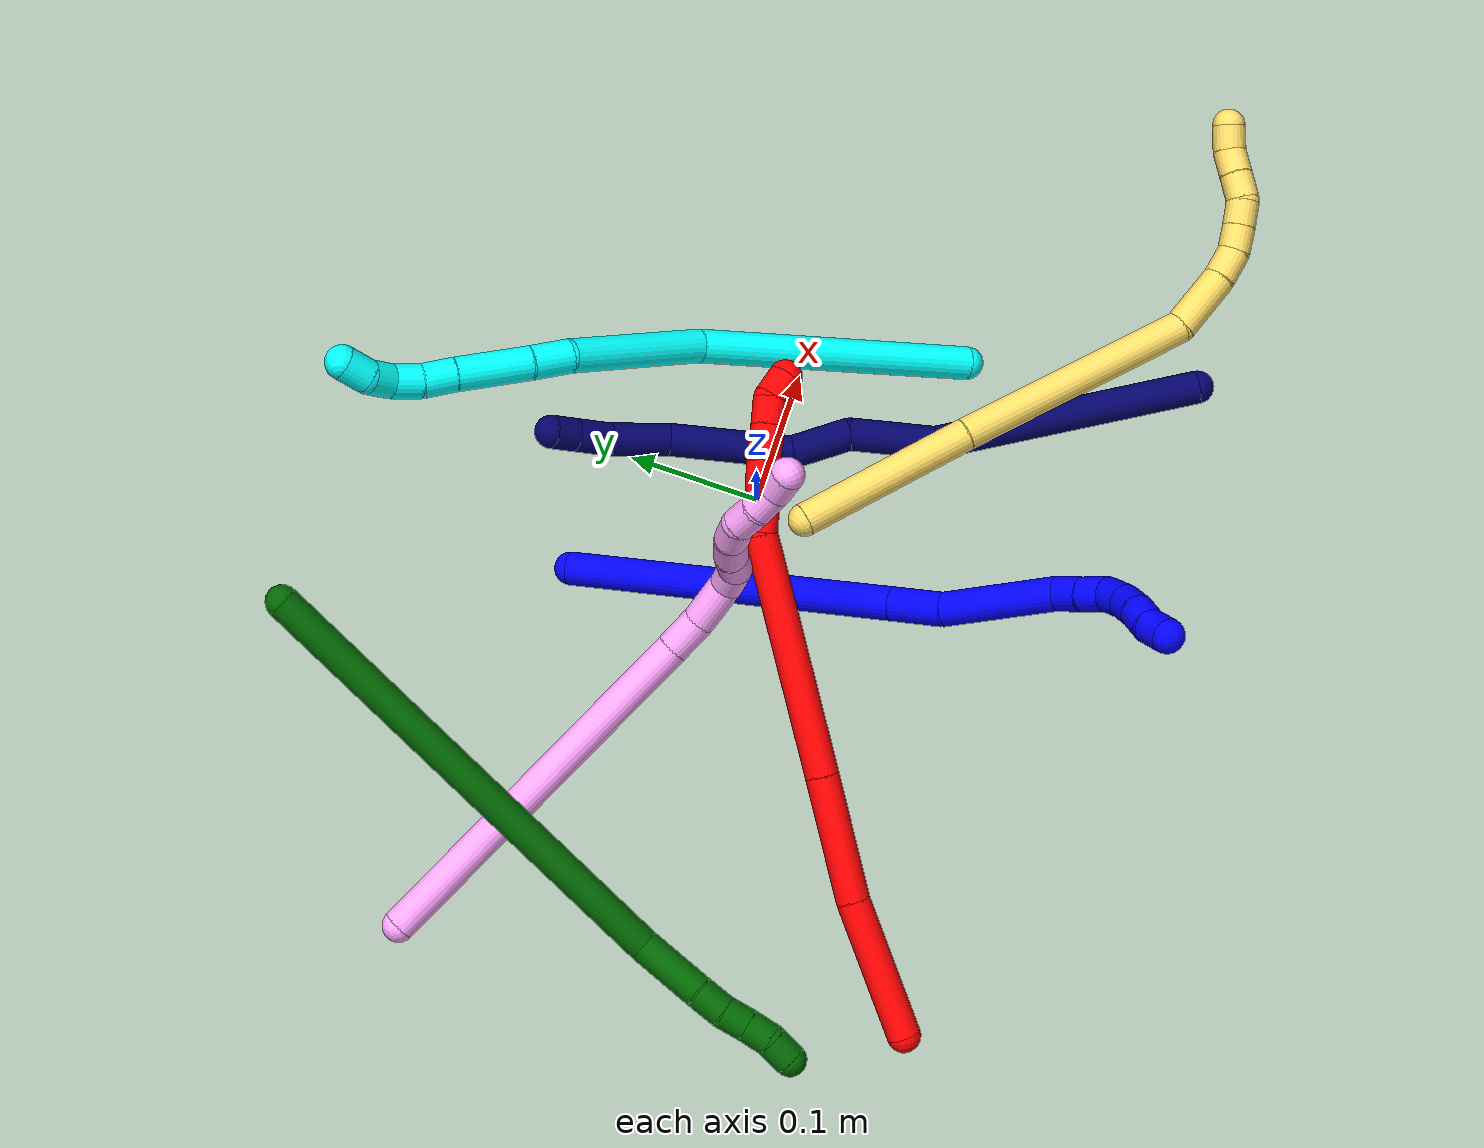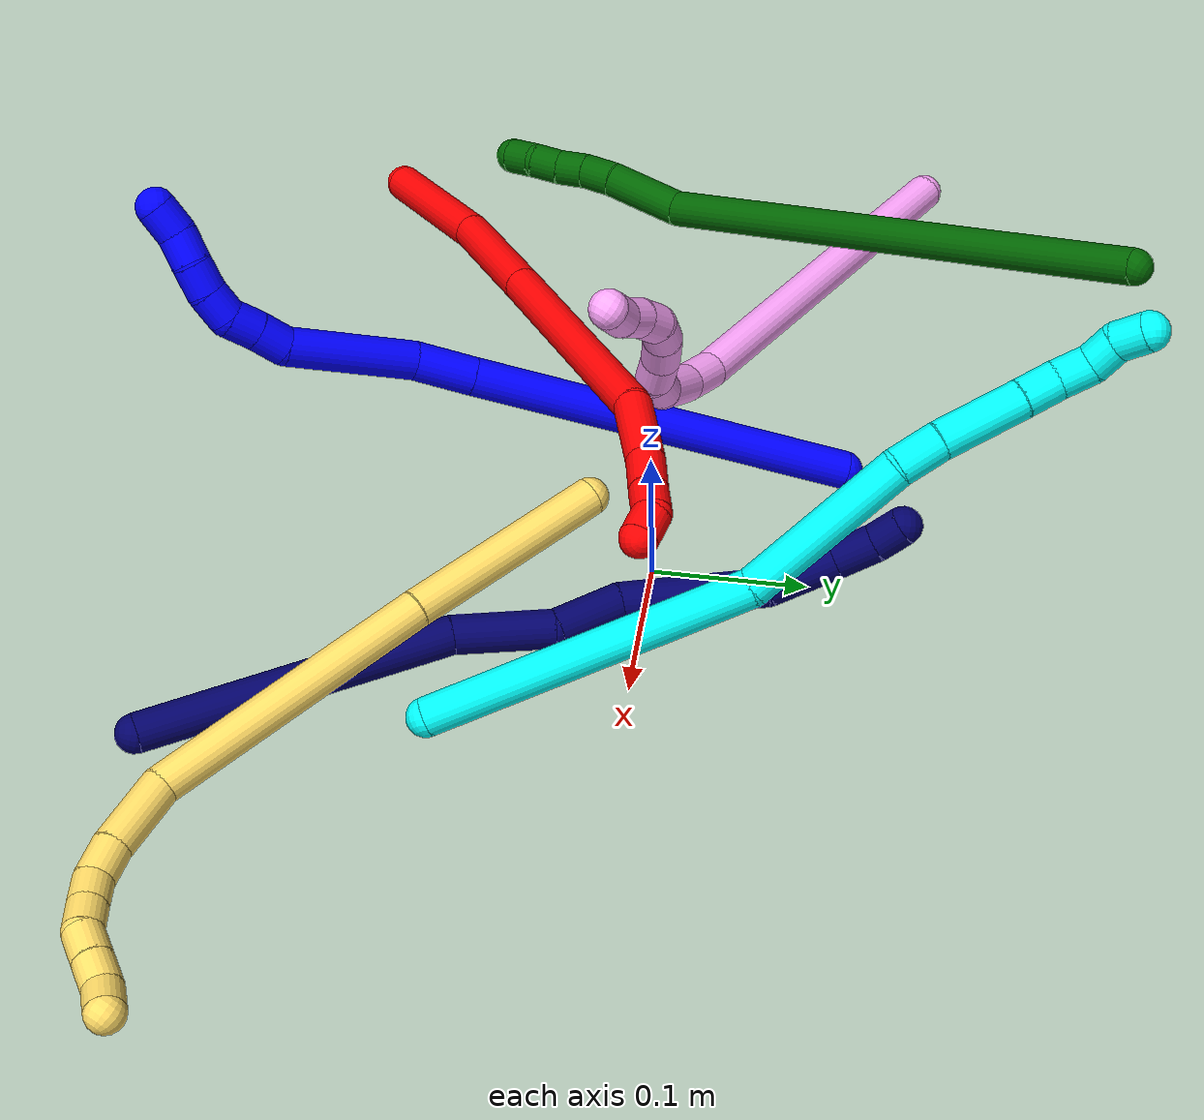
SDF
<sdf version="1.7">
 <world name="default">
  <plugin name="TubeGeneratorPlugin" filename="libtube_generator_plugin.so"/>
  <model name="photoneo_s_sensor">
   <static>1</static>
   <pose>0 0 2 1.57079 1.57079 3.14159</pose>
   <link name="link">
    <inertial><mass>0.1</mass></inertial>
    <sensor name="sensor" type="depth">
     <update_rate>30</update_rate>
     <camera>
      <horizontal_fov>1.22</horizontal_fov>
      <image><width>1920</width><height>1200</height><format>B8G8R8</format></image>
      <clip><near>0.1</near><far>4</far></clip>
      <depth_camera><output>points</output></depth_camera>
     </camera>
     <plugin name="camera_plugin" filename="libgazebo_ros_depth_camera.so">
      <baseline>0.2</baseline>
      <alwaysOn>1</alwaysOn>
      <updateRate>0.0</updateRate>
      <cameraName>camera_ir</cameraName>
      <imageTopicName>/camera/color/image_raw</imageTopicName>
      <cameraInfoTopicName>/camera/color/camera_info</cameraInfoTopicName>
      <depthImageTopicName>/camera/depth/image_raw</depthImageTopicName>
      <depthImageCameraInfoTopicName>/camera/depth/camera_info</depthImageCameraInfoTopicName>
      <pointCloudTopicName>/camera/depth/points</pointCloudTopicName>
      <frameName>fr_optical</frameName>
      <pointCloudCutoff>0.1</pointCloudCutoff>
      <pointCloudCutoffMax>2.0</pointCloudCutoffMax>
      <distortionK1>0</distortionK1>
      <distortionK2>0</distortionK2>
      <distortionK3>0</distortionK3>
      <distortionT1>0</distortionT1>
      <distortionT2>0</distortionT2>
      <CxPrime>0</CxPrime>
      <Cx>0</Cx>
      <Cy>0</Cy>
      <focalLength>0</focalLength>
      <hackBaseline>0</hackBaseline>
     </plugin>
    </sensor>
   </link>
  </model>
  <gravity>0 0 -9.8</gravity>
  <magnetic_field>6e-06 2.3e-05 -4.2e-05</magnetic_field>
  <atmosphere type="adiabatic"/>
  <physics name="default_physics" default="0" type="ode">
   <max_step_size>0.003</max_step_size>
   <real_time_factor>1</real_time_factor>
   <real_time_update_rate>1000</real_time_update_rate>
   <max_contacts>10000</max_contacts>
   <ode>
    <solver>
     <type>quick</type>
     <iters>100</iters>
     <sor>1.3</sor>
     <use_dynamic_moi_rescaling>0</use_dynamic_moi_rescaling>
    </solver>
    <constraints>
     <contact_max_correcting_vel>0</contact_max_correcting_vel>
     <contact_surface_layer>0.001</contact_surface_layer>
     <cfm>0</cfm>
     <erp>0.2</erp>
    </constraints>
   </ode>
  </physics>
  <scene><ambient>0.4 0.4 0.4 1</ambient><background>0.7 0.7 0.7 1</background><shadows>0</shadows></scene>
  <audio><device>default</device></audio>
  <spherical_coordinates>
   <surface_model>EARTH_WGS84</surface_model>
   <latitude_deg>0</latitude_deg>
   <longitude_deg>0</longitude_deg>
   <elevation>0</elevation>
   <heading_deg>0</heading_deg>
  </spherical_coordinates>
  <model name="bin">
   <static>1</static>
   <link name="bottom">
    <collision name="collision-bottom">
     <pose>0 0 -0.01 0 -0 0</pose>
     <geometry><box><size>0.8 0.6 0.02</size></box></geometry>
     <surface>
      <friction><ode><mu>100</mu><mu2>100</mu2></ode></friction>
      <contact><collide_bitmask>65535</collide_bitmask></contact>
     </surface>
    </collision>
   </link>
   <link name="west_wall">
    <collision name="collision-west_wall">
     <pose>-0.41 0 0.1 0 -0 0</pose>
     <geometry><box><size>0.02 0.6 0.2</size></box></geometry>
     <surface>
      <friction><ode><mu>100</mu><mu2>100</mu2></ode></friction>
      <contact><collide_bitmask>65535</collide_bitmask></contact>
     </surface>
    </collision>
   </link>
   <link name="east_wall">
    <collision name="collision-east_wall">
     <pose>0.41 0 0.1 0 -0 0</pose>
     <geometry><box><size>0.02 0.6 0.2</size></box></geometry>
     <surface>
      <friction><ode><mu>100</mu><mu2>100</mu2></ode></friction>
      <contact><collide_bitmask>65535</collide_bitmask></contact>
     </surface>
    </collision>
   </link>
   <link name="south_wall">
    <collision name="collision-south_wall">
     <pose>0 -0.31 0.1 0 -0 0</pose>
     <geometry><box><size>0.8 0.02 0.2</size></box></geometry>
     <surface>
      <friction><ode><mu>100</mu><mu2>100</mu2></ode></friction>
      <contact><collide_bitmask>65535</collide_bitmask></contact>
     </surface>
    </collision>
   </link>
   <link name="north_wall">
    <collision name="collision-north_wall">
     <pose>0 0.31 0.1 0 -0 0</pose>
     <geometry><box><size>0.8 0.02 0.2</size></box></geometry>
     <surface>
      <friction><ode><mu>100</mu><mu2>100</mu2></ode></friction>
      <contact><collide_bitmask>65535</collide_bitmask></contact>
     </surface>
    </collision>
   </link>
  </model>
  <model name="1">
   <static>0</static>
   <link name="1">
    <collision name="collision-cylinder-e_1_1_4">
     <pose>0.011053 -0.040038 0.120317 0.321242 0.086943 0.014095</pose>
     <geometry><cylinder><radius>0.0125</radius><length>0.254569</length></cylinder></geometry>
     <surface>
      <friction><ode><mu>1.16</mu><mu2>1.16</mu2><slip1>0</slip1><slip2>0</slip2></ode></friction>
      <contact><ode><kp>1e+06</kp><kd>1</kd><max_vel>0</max_vel><min_depth>0.001</min_depth></ode></contact>
     </surface>
    </collision>
    <visual name="visual-cylinder-e_1_1_4">
     <pose>0.011053 -0.040038 0.120317 0.321242 0.086943 0.014095</pose>
     <geometry><cylinder><radius>0.0125</radius><length>0.254569</length></cylinder></geometry>
     <material><ambient>0 0 1 1</ambient></material>
    </visual>
    <collision name="collision-cylinder-e_2_4_5">
     <pose>0.023717 -0.086509 0.258992 0.337076 0.082693 0.014078</pose>
     <geometry><cylinder><radius>0.0125</radius><length>0.03904</length></cylinder></geometry>
     <surface>
      <friction><ode><mu>1.16</mu><mu2>1.16</mu2><slip1>0</slip1><slip2>0</slip2></ode></friction>
      <contact><ode><kp>1e+06</kp><kd>1</kd><max_vel>0</max_vel><min_depth>0.001</min_depth></ode></contact>
     </surface>
    </collision>
    <visual name="visual-cylinder-e_2_4_5">
     <pose>0.023717 -0.086509 0.258992 0.337076 0.082693 0.014078</pose>
     <geometry><cylinder><radius>0.0125</radius><length>0.03904</length></cylinder></geometry>
     <material><ambient>0 0 1 1</ambient></material>
    </visual>
    <collision name="collision-cylinder-e_3_5_6">
     <pose>0.020078 -0.101813 0.318766 0.211002 -0.123377 -0.013081</pose>
     <geometry><cylinder><radius>0.0125</radius><length>0.085358</length></cylinder></geometry>
     <surface>
      <friction><ode><mu>1.16</mu><mu2>1.16</mu2><slip1>0</slip1><slip2>0</slip2></ode></friction>
      <contact><ode><kp>1e+06</kp><kd>1</kd><max_vel>0</max_vel><min_depth>0.001</min_depth></ode></contact>
     </surface>
    </collision>
    <visual name="visual-cylinder-e_3_5_6">
     <pose>0.020078 -0.101813 0.318766 0.211002 -0.123377 -0.013081</pose>
     <geometry><cylinder><radius>0.0125</radius><length>0.085358</length></cylinder></geometry>
     <material><ambient>0 0 1 1</ambient></material>
    </visual>
    <collision name="collision-cylinder-e_4_6_7">
     <pose>0.013742 -0.11657 0.368823 0.597901 -0.103242 -0.031843</pose>
     <geometry><cylinder><radius>0.0125</radius><length>0.021024</length></cylinder></geometry>
     <surface>
      <friction><ode><mu>1.16</mu><mu2>1.16</mu2><slip1>0</slip1><slip2>0</slip2></ode></friction>
      <contact><ode><kp>1e+06</kp><kd>1</kd><max_vel>0</max_vel><min_depth>0.001</min_depth></ode></contact>
     </surface>
    </collision>
    <visual name="visual-cylinder-e_4_6_7">
     <pose>0.013742 -0.11657 0.368823 0.597901 -0.103242 -0.031843</pose>
     <geometry><cylinder><radius>0.0125</radius><length>0.021024</length></cylinder></geometry>
     <material><ambient>0 0 1 1</ambient></material>
    </visual>
    <collision name="collision-cylinder-e_5_7_8">
     <pose>0.01142 -0.127309 0.386124 0.510886 -0.124165 -0.032464</pose>
     <geometry><cylinder><radius>0.0125</radius><length>0.020006</length></cylinder></geometry>
     <surface>
      <friction><ode><mu>1.16</mu><mu2>1.16</mu2><slip1>0</slip1><slip2>0</slip2></ode></friction>
      <contact><ode><kp>1e+06</kp><kd>1</kd><max_vel>0</max_vel><min_depth>0.001</min_depth></ode></contact>
     </surface>
    </collision>
    <visual name="visual-cylinder-e_5_7_8">
     <pose>0.01142 -0.127309 0.386124 0.510886 -0.124165 -0.032464</pose>
     <geometry><cylinder><radius>0.0125</radius><length>0.020006</length></cylinder></geometry>
     <material><ambient>0 0 1 1</ambient></material>
    </visual>
    <collision name="collision-cylinder-e_6_8_9">
     <pose>0.010165 -0.14036 0.40051 0.960894 -0.001627 -0.000848</pose>
     <geometry><cylinder><radius>0.0125</radius><length>0.020001</length></cylinder></geometry>
     <surface>
      <friction><ode><mu>1.16</mu><mu2>1.16</mu2><slip1>0</slip1><slip2>0</slip2></ode></friction>
      <contact><ode><kp>1e+06</kp><kd>1</kd><max_vel>0</max_vel><min_depth>0.001</min_depth></ode></contact>
     </surface>
    </collision>
    <visual name="visual-cylinder-e_6_8_9">
     <pose>0.010165 -0.14036 0.40051 0.960894 -0.001627 -0.000848</pose>
     <geometry><cylinder><radius>0.0125</radius><length>0.020001</length></cylinder></geometry>
     <material><ambient>0 0 1 1</ambient></material>
    </visual>
    <collision name="collision-cylinder-e_7_9_10">
     <pose>0.010445 -0.157724 0.410227 1.1604 0.029705 0.019471</pose>
     <geometry><cylinder><radius>0.0125</radius><length>0.020003</length></cylinder></geometry>
     <surface>
      <friction><ode><mu>1.16</mu><mu2>1.16</mu2><slip1>0</slip1><slip2>0</slip2></ode></friction>
      <contact><ode><kp>1e+06</kp><kd>1</kd><max_vel>0</max_vel><min_depth>0.001</min_depth></ode></contact>
     </surface>
    </collision>
    <visual name="visual-cylinder-e_7_9_10">
     <pose>0.010445 -0.157724 0.410227 1.1604 0.029705 0.019471</pose>
     <geometry><cylinder><radius>0.0125</radius><length>0.020003</length></cylinder></geometry>
     <material><ambient>0 0 1 1</ambient></material>
    </visual>
    <collision name="collision-cylinder-e_8_10_11">
     <pose>0.012685 -0.176053 0.41772 1.20548 0.195539 0.134789</pose>
     <geometry><cylinder><radius>0.0125</radius><length>0.02</length></cylinder></geometry>
     <surface>
      <friction><ode><mu>1.16</mu><mu2>1.16</mu2><slip1>0</slip1><slip2>0</slip2></ode></friction>
      <contact><ode><kp>1e+06</kp><kd>1</kd><max_vel>0</max_vel><min_depth>0.001</min_depth></ode></contact>
     </surface>
    </collision>
    <visual name="visual-cylinder-e_8_10_11">
     <pose>0.012685 -0.176053 0.41772 1.20548 0.195539 0.134789</pose>
     <geometry><cylinder><radius>0.0125</radius><length>0.02</length></cylinder></geometry>
     <material><ambient>0 0 1 1</ambient></material>
    </visual>
    <collision name="collision-cylinder-e_9_11_2">
     <pose>0.015436 -0.193463 0.426821 0.974637 0.080835 0.042855</pose>
     <geometry><cylinder><radius>0.0125</radius><length>0.02</length></cylinder></geometry>
     <surface>
      <friction><ode><mu>1.16</mu><mu2>1.16</mu2><slip1>0</slip1><slip2>0</slip2></ode></friction>
      <contact><ode><kp>1e+06</kp><kd>1</kd><max_vel>0</max_vel><min_depth>0.001</min_depth></ode></contact>
     </surface>
    </collision>
    <visual name="visual-cylinder-e_9_11_2">
     <pose>0.015436 -0.193463 0.426821 0.974637 0.080835 0.042855</pose>
     <geometry><cylinder><radius>0.0125</radius><length>0.02</length></cylinder></geometry>
     <material><ambient>0 0 1 1</ambient></material>
    </visual>
    <collision name="collision-sphere-2">
     <pose>0.016243 -0.201711 0.432417 0 -0 0</pose>
     <geometry><sphere><radius>0.0125</radius></sphere></geometry>
     <surface>
      <friction><ode><mu>1.16</mu><mu2>1.16</mu2><slip1>0</slip1><slip2>0</slip2></ode></friction>
      <contact><ode><kp>1e+06</kp><kd>1</kd><max_vel>0</max_vel><min_depth>0.001</min_depth></ode></contact>
     </surface>
    </collision>
    <visual name="visual-sphere-2">
     <pose>0.016243 -0.201711 0.432417 0 -0 0</pose>
     <geometry><sphere><radius>0.0125</radius></sphere></geometry>
     <material><ambient>0 0 1 1</ambient></material>
    </visual>
    <collision name="collision-sphere-11">
     <pose>0.014628 -0.185215 0.421224 0 -0 0</pose>
     <geometry><sphere><radius>0.0125</radius></sphere></geometry>
     <surface>
      <friction><ode><mu>1.16</mu><mu2>1.16</mu2><slip1>0</slip1><slip2>0</slip2></ode></friction>
      <contact><ode><kp>1e+06</kp><kd>1</kd><max_vel>0</max_vel><min_depth>0.001</min_depth></ode></contact>
     </surface>
    </collision>
    <visual name="visual-sphere-11">
     <pose>0.014628 -0.185215 0.421224 0 -0 0</pose>
     <geometry><sphere><radius>0.0125</radius></sphere></geometry>
     <material><ambient>0 0 1 1</ambient></material>
    </visual>
    <collision name="collision-sphere-10">
     <pose>0.010742 -0.166891 0.414215 0 -0 0</pose>
     <geometry><sphere><radius>0.0125</radius></sphere></geometry>
     <surface>
      <friction><ode><mu>1.16</mu><mu2>1.16</mu2><slip1>0</slip1><slip2>0</slip2></ode></friction>
      <contact><ode><kp>1e+06</kp><kd>1</kd><max_vel>0</max_vel><min_depth>0.001</min_depth></ode></contact>
     </surface>
    </collision>
    <visual name="visual-sphere-10">
     <pose>0.010742 -0.166891 0.414215 0 -0 0</pose>
     <geometry><sphere><radius>0.0125</radius></sphere></geometry>
     <material><ambient>0 0 1 1</ambient></material>
    </visual>
    <collision name="collision-sphere-9">
     <pose>0.010148 -0.148557 0.406239 0 -0 0</pose>
     <geometry><sphere><radius>0.0125</radius></sphere></geometry>
     <surface>
      <friction><ode><mu>1.16</mu><mu2>1.16</mu2><slip1>0</slip1><slip2>0</slip2></ode></friction>
      <contact><ode><kp>1e+06</kp><kd>1</kd><max_vel>0</max_vel><min_depth>0.001</min_depth></ode></contact>
     </surface>
    </collision>
    <visual name="visual-sphere-9">
     <pose>0.010148 -0.148557 0.406239 0 -0 0</pose>
     <geometry><sphere><radius>0.0125</radius></sphere></geometry>
     <material><ambient>0 0 1 1</ambient></material>
    </visual>
    <collision name="collision-sphere-4">
     <pose>0.022105 -0.080075 0.240634 0 -0 0</pose>
     <geometry><sphere><radius>0.0125</radius></sphere></geometry>
     <surface>
      <friction><ode><mu>1.16</mu><mu2>1.16</mu2><slip1>0</slip1><slip2>0</slip2></ode></friction>
      <contact><ode><kp>1e+06</kp><kd>1</kd><max_vel>0</max_vel><min_depth>0.001</min_depth></ode></contact>
     </surface>
    </collision>
    <visual name="visual-sphere-4">
     <pose>0.022105 -0.080075 0.240634 0 -0 0</pose>
     <geometry><sphere><radius>0.0125</radius></sphere></geometry>
     <material><ambient>0 0 1 1</ambient></material>
    </visual>
    <collision name="collision-sphere-1">
     <geometry><sphere><radius>0.0125</radius></sphere></geometry>
     <surface>
      <friction><ode><mu>1.16</mu><mu2>1.16</mu2><slip1>0</slip1><slip2>0</slip2></ode></friction>
      <contact><ode><kp>1e+06</kp><kd>1</kd><max_vel>0</max_vel><min_depth>0.001</min_depth></ode></contact>
     </surface>
    </collision>
    <visual name="visual-sphere-1">
     <geometry><sphere><radius>0.0125</radius></sphere></geometry>
     <material><ambient>0 0 1 1</ambient></material>
    </visual>
    <collision name="collision-sphere-8">
     <pose>0.010181 -0.132162 0.394782 0 -0 0</pose>
     <geometry><sphere><radius>0.0125</radius></sphere></geometry>
     <surface>
      <friction><ode><mu>1.16</mu><mu2>1.16</mu2><slip1>0</slip1><slip2>0</slip2></ode></friction>
      <contact><ode><kp>1e+06</kp><kd>1</kd><max_vel>0</max_vel><min_depth>0.001</min_depth></ode></contact>
     </surface>
    </collision>
    <visual name="visual-sphere-8">
     <pose>0.010181 -0.132162 0.394782 0 -0 0</pose>
     <geometry><sphere><radius>0.0125</radius></sphere></geometry>
     <material><ambient>0 0 1 1</ambient></material>
    </visual>
    <collision name="collision-sphere-5">
     <pose>0.02533 -0.092943 0.277351 0 -0 0</pose>
     <geometry><sphere><radius>0.0125</radius></sphere></geometry>
     <surface>
      <friction><ode><mu>1.16</mu><mu2>1.16</mu2><slip1>0</slip1><slip2>0</slip2></ode></friction>
      <contact><ode><kp>1e+06</kp><kd>1</kd><max_vel>0</max_vel><min_depth>0.001</min_depth></ode></contact>
     </surface>
    </collision>
    <visual name="visual-sphere-5">
     <pose>0.02533 -0.092943 0.277351 0 -0 0</pose>
     <geometry><sphere><radius>0.0125</radius></sphere></geometry>
     <material><ambient>0 0 1 1</ambient></material>
    </visual>
    <collision name="collision-sphere-6">
     <pose>0.014825 -0.110684 0.360181 0 -0 0</pose>
     <geometry><sphere><radius>0.0125</radius></sphere></geometry>
     <surface>
      <friction><ode><mu>1.16</mu><mu2>1.16</mu2><slip1>0</slip1><slip2>0</slip2></ode></friction>
      <contact><ode><kp>1e+06</kp><kd>1</kd><max_vel>0</max_vel><min_depth>0.001</min_depth></ode></contact>
     </surface>
    </collision>
    <visual name="visual-sphere-6">
     <pose>0.014825 -0.110684 0.360181 0 -0 0</pose>
     <geometry><sphere><radius>0.0125</radius></sphere></geometry>
     <material><ambient>0 0 1 1</ambient></material>
    </visual>
    <collision name="collision-sphere-7">
     <pose>0.012659 -0.122456 0.377465 0 -0 0</pose>
     <geometry><sphere><radius>0.0125</radius></sphere></geometry>
     <surface>
      <friction><ode><mu>1.16</mu><mu2>1.16</mu2><slip1>0</slip1><slip2>0</slip2></ode></friction>
      <contact><ode><kp>1e+06</kp><kd>1</kd><max_vel>0</max_vel><min_depth>0.001</min_depth></ode></contact>
     </surface>
    </collision>
    <visual name="visual-sphere-7">
     <pose>0.012659 -0.122456 0.377465 0 -0 0</pose>
     <geometry><sphere><radius>0.0125</radius></sphere></geometry>
     <material><ambient>0 0 1 1</ambient></material>
    </visual>
    <inertial>
     <pose>0.013891 -0.081221 0.23307 0 -0 0</pose>
     <mass>0.5</mass>
     <inertia>
      <ixx>0.00147</ixx>
      <ixy>0</ixy>
      <ixz>0</ixz>
      <iyy>0.001383</iyy>
      <iyz>0</iyz>
      <izz>0.000376</izz>
     </inertia>
    </inertial>
   </link>
   <pose>-0.096905 0.113647 0.011495 -1.41684 0.556129 -2.64975</pose>
  </model>
  <model name="2">
   <static>0</static>
   <link name="2">
    <collision name="collision-cylinder-e_1_1_4">
     <pose>0.021224 0.005028 -0.04859 -3.03849 0.409868 -2.65495</pose>
     <geometry><cylinder><radius>0.0125</radius><length>0.106522</length></cylinder></geometry>
     <surface>
      <friction><ode><mu>1.16</mu><mu2>1.16</mu2><slip1>0</slip1><slip2>0</slip2></ode></friction>
      <contact><ode><kp>1e+06</kp><kd>1</kd><max_vel>0</max_vel><min_depth>0.001</min_depth></ode></contact>
     </surface>
    </collision>
    <visual name="visual-cylinder-e_1_1_4">
     <pose>0.021224 0.005028 -0.04859 -3.03849 0.409868 -2.65495</pose>
     <geometry><cylinder><radius>0.0125</radius><length>0.106522</length></cylinder></geometry>
     <material><ambient>1 0 0 1</ambient></material>
    </visual>
    <collision name="collision-cylinder-e_2_4_5">
     <pose>0.057779 0.018836 -0.140716 -2.94257 0.332403 -2.06785</pose>
     <geometry><cylinder><radius>0.0125</radius><length>0.093969</length></cylinder></geometry>
     <surface>
      <friction><ode><mu>1.16</mu><mu2>1.16</mu2><slip1>0</slip1><slip2>0</slip2></ode></friction>
      <contact><ode><kp>1e+06</kp><kd>1</kd><max_vel>0</max_vel><min_depth>0.001</min_depth></ode></contact>
     </surface>
    </collision>
    <visual name="visual-cylinder-e_2_4_5">
     <pose>0.057779 0.018836 -0.140716 -2.94257 0.332403 -2.06785</pose>
     <geometry><cylinder><radius>0.0125</radius><length>0.093969</length></cylinder></geometry>
     <material><ambient>1 0 0 1</ambient></material>
    </visual>
    <collision name="collision-cylinder-e_3_5_6">
     <pose>0.104117 0.045667 -0.266436 -2.9254 0.353045 -2.0485</pose>
     <geometry><cylinder><radius>0.0125</radius><length>0.179348</length></cylinder></geometry>
     <surface>
      <friction><ode><mu>1.16</mu><mu2>1.16</mu2><slip1>0</slip1><slip2>0</slip2></ode></friction>
      <contact><ode><kp>1e+06</kp><kd>1</kd><max_vel>0</max_vel><min_depth>0.001</min_depth></ode></contact>
     </surface>
    </collision>
    <visual name="visual-cylinder-e_3_5_6">
     <pose>0.104117 0.045667 -0.266436 -2.9254 0.353045 -2.0485</pose>
     <geometry><cylinder><radius>0.0125</radius><length>0.179348</length></cylinder></geometry>
     <material><ambient>1 0 0 1</ambient></material>
    </visual>
    <collision name="collision-cylinder-e_4_6_7">
     <pose>0.140779 0.076719 -0.370862 -2.61255 0.216169 -0.762028</pose>
     <geometry><cylinder><radius>0.0125</radius><length>0.052754</length></cylinder></geometry>
     <surface>
      <friction><ode><mu>1.16</mu><mu2>1.16</mu2><slip1>0</slip1><slip2>0</slip2></ode></friction>
      <contact><ode><kp>1e+06</kp><kd>1</kd><max_vel>0</max_vel><min_depth>0.001</min_depth></ode></contact>
     </surface>
    </collision>
    <visual name="visual-cylinder-e_4_6_7">
     <pose>0.140779 0.076719 -0.370862 -2.61255 0.216169 -0.762028</pose>
     <geometry><cylinder><radius>0.0125</radius><length>0.052754</length></cylinder></geometry>
     <material><ambient>1 0 0 1</ambient></material>
    </visual>
    <collision name="collision-cylinder-e_5_7_8">
     <pose>0.148341 0.096964 -0.404221 -2.56427 0.14252 -0.471805</pose>
     <geometry><cylinder><radius>0.0125</radius><length>0.026809</length></cylinder></geometry>
     <surface>
      <friction><ode><mu>1.16</mu><mu2>1.16</mu2><slip1>0</slip1><slip2>0</slip2></ode></friction>
      <contact><ode><kp>1e+06</kp><kd>1</kd><max_vel>0</max_vel><min_depth>0.001</min_depth></ode></contact>
     </surface>
    </collision>
    <visual name="visual-cylinder-e_5_7_8">
     <pose>0.148341 0.096964 -0.404221 -2.56427 0.14252 -0.471805</pose>
     <geometry><cylinder><radius>0.0125</radius><length>0.026809</length></cylinder></geometry>
     <material><ambient>1 0 0 1</ambient></material>
    </visual>
    <collision name="collision-cylinder-e_6_8_9">
     <pose>0.152097 0.109674 -0.423827 -2.5693 0.181403 -0.599619</pose>
     <geometry><cylinder><radius>0.0125</radius><length>0.020531</length></cylinder></geometry>
     <surface>
      <friction><ode><mu>1.16</mu><mu2>1.16</mu2><slip1>0</slip1><slip2>0</slip2></ode></friction>
      <contact><ode><kp>1e+06</kp><kd>1</kd><max_vel>0</max_vel><min_depth>0.001</min_depth></ode></contact>
     </surface>
    </collision>
    <visual name="visual-cylinder-e_6_8_9">
     <pose>0.152097 0.109674 -0.423827 -2.5693 0.181403 -0.599619</pose>
     <geometry><cylinder><radius>0.0125</radius><length>0.020531</length></cylinder></geometry>
     <material><ambient>1 0 0 1</ambient></material>
    </visual>
    <collision name="collision-cylinder-e_7_9_2">
     <pose>0.152179 0.123189 -0.438042 -2.18932 -0.177263 0.341276</pose>
     <geometry><cylinder><radius>0.0125</radius><length>0.020068</length></cylinder></geometry>
     <surface>
      <friction><ode><mu>1.16</mu><mu2>1.16</mu2><slip1>0</slip1><slip2>0</slip2></ode></friction>
      <contact><ode><kp>1e+06</kp><kd>1</kd><max_vel>0</max_vel><min_depth>0.001</min_depth></ode></contact>
     </surface>
    </collision>
    <visual name="visual-cylinder-e_7_9_2">
     <pose>0.152179 0.123189 -0.438042 -2.18932 -0.177263 0.341276</pose>
     <geometry><cylinder><radius>0.0125</radius><length>0.020068</length></cylinder></geometry>
     <material><ambient>1 0 0 1</ambient></material>
    </visual>
    <collision name="collision-sphere-2">
     <pose>0.15041 0.131236 -0.443769 0 -0 0</pose>
     <geometry><sphere><radius>0.0125</radius></sphere></geometry>
     <surface>
      <friction><ode><mu>1.16</mu><mu2>1.16</mu2><slip1>0</slip1><slip2>0</slip2></ode></friction>
      <contact><ode><kp>1e+06</kp><kd>1</kd><max_vel>0</max_vel><min_depth>0.001</min_depth></ode></contact>
     </surface>
    </collision>
    <visual name="visual-sphere-2">
     <pose>0.15041 0.131236 -0.443769 0 -0 0</pose>
     <geometry><sphere><radius>0.0125</radius></sphere></geometry>
     <material><ambient>1 0 0 1</ambient></material>
    </visual>
    <collision name="collision-sphere-9">
     <pose>0.153949 0.115142 -0.432315 0 -0 0</pose>
     <geometry><sphere><radius>0.0125</radius></sphere></geometry>
     <surface>
      <friction><ode><mu>1.16</mu><mu2>1.16</mu2><slip1>0</slip1><slip2>0</slip2></ode></friction>
      <contact><ode><kp>1e+06</kp><kd>1</kd><max_vel>0</max_vel><min_depth>0.001</min_depth></ode></contact>
     </surface>
    </collision>
    <visual name="visual-sphere-9">
     <pose>0.153949 0.115142 -0.432315 0 -0 0</pose>
     <geometry><sphere><radius>0.0125</radius></sphere></geometry>
     <material><ambient>1 0 0 1</ambient></material>
    </visual>
    <collision name="collision-sphere-4">
     <pose>0.042448 0.010055 -0.09718 0 -0 0</pose>
     <geometry><sphere><radius>0.0125</radius></sphere></geometry>
     <surface>
      <friction><ode><mu>1.16</mu><mu2>1.16</mu2><slip1>0</slip1><slip2>0</slip2></ode></friction>
      <contact><ode><kp>1e+06</kp><kd>1</kd><max_vel>0</max_vel><min_depth>0.001</min_depth></ode></contact>
     </surface>
    </collision>
    <visual name="visual-sphere-4">
     <pose>0.042448 0.010055 -0.09718 0 -0 0</pose>
     <geometry><sphere><radius>0.0125</radius></sphere></geometry>
     <material><ambient>1 0 0 1</ambient></material>
    </visual>
    <collision name="collision-sphere-1">
     <geometry><sphere><radius>0.0125</radius></sphere></geometry>
     <surface>
      <friction><ode><mu>1.16</mu><mu2>1.16</mu2><slip1>0</slip1><slip2>0</slip2></ode></friction>
      <contact><ode><kp>1e+06</kp><kd>1</kd><max_vel>0</max_vel><min_depth>0.001</min_depth></ode></contact>
     </surface>
    </collision>
    <visual name="visual-sphere-1">
     <geometry><sphere><radius>0.0125</radius></sphere></geometry>
     <material><ambient>1 0 0 1</ambient></material>
    </visual>
    <collision name="collision-sphere-8">
     <pose>0.150245 0.104206 -0.415339 0 -0 0</pose>
     <geometry><sphere><radius>0.0125</radius></sphere></geometry>
     <surface>
      <friction><ode><mu>1.16</mu><mu2>1.16</mu2><slip1>0</slip1><slip2>0</slip2></ode></friction>
      <contact><ode><kp>1e+06</kp><kd>1</kd><max_vel>0</max_vel><min_depth>0.001</min_depth></ode></contact>
     </surface>
    </collision>
    <visual name="visual-sphere-8">
     <pose>0.150245 0.104206 -0.415339 0 -0 0</pose>
     <geometry><sphere><radius>0.0125</radius></sphere></geometry>
     <material><ambient>1 0 0 1</ambient></material>
    </visual>
    <collision name="collision-sphere-5">
     <pose>0.073111 0.027617 -0.184252 0 -0 0</pose>
     <geometry><sphere><radius>0.0125</radius></sphere></geometry>
     <surface>
      <friction><ode><mu>1.16</mu><mu2>1.16</mu2><slip1>0</slip1><slip2>0</slip2></ode></friction>
      <contact><ode><kp>1e+06</kp><kd>1</kd><max_vel>0</max_vel><min_depth>0.001</min_depth></ode></contact>
     </surface>
    </collision>
    <visual name="visual-sphere-5">
     <pose>0.073111 0.027617 -0.184252 0 -0 0</pose>
     <geometry><sphere><radius>0.0125</radius></sphere></geometry>
     <material><ambient>1 0 0 1</ambient></material>
    </visual>
    <collision name="collision-sphere-6">
     <pose>0.135122 0.063717 -0.348621 0 -0 0</pose>
     <geometry><sphere><radius>0.0125</radius></sphere></geometry>
     <surface>
      <friction><ode><mu>1.16</mu><mu2>1.16</mu2><slip1>0</slip1><slip2>0</slip2></ode></friction>
      <contact><ode><kp>1e+06</kp><kd>1</kd><max_vel>0</max_vel><min_depth>0.001</min_depth></ode></contact>
     </surface>
    </collision>
    <visual name="visual-sphere-6">
     <pose>0.135122 0.063717 -0.348621 0 -0 0</pose>
     <geometry><sphere><radius>0.0125</radius></sphere></geometry>
     <material><ambient>1 0 0 1</ambient></material>
    </visual>
    <collision name="collision-sphere-7">
     <pose>0.146437 0.089722 -0.393103 0 -0 0</pose>
     <geometry><sphere><radius>0.0125</radius></sphere></geometry>
     <surface>
      <friction><ode><mu>1.16</mu><mu2>1.16</mu2><slip1>0</slip1><slip2>0</slip2></ode></friction>
      <contact><ode><kp>1e+06</kp><kd>1</kd><max_vel>0</max_vel><min_depth>0.001</min_depth></ode></contact>
     </surface>
    </collision>
    <visual name="visual-sphere-7">
     <pose>0.146437 0.089722 -0.393103 0 -0 0</pose>
     <geometry><sphere><radius>0.0125</radius></sphere></geometry>
     <material><ambient>1 0 0 1</ambient></material>
    </visual>
    <inertial>
     <pose>0.087887 0.043733 -0.228154 0 -0 0</pose>
     <mass>0.5</mass>
     <inertia>
      <ixx>-0.000825</ixx>
      <ixy>0</ixy>
      <ixz>0</ixz>
      <iyy>-0.000141</iyy>
      <iyz>0</iyz>
      <izz>-0.000404</izz>
     </inertia>
    </inertial>
   </link>
   <pose>-0.345363 -0.230359 0.012492 -2.30082 0.536684 1.57643</pose>
  </model>
  <model name="3">
   <static>0</static>
   <link name="3">
    <collision name="collision-cylinder-e_1_1_4">
     <pose>-0.036321 0.097602 0.021806 -1.35099 -0.348364 0.280132</pose>
     <geometry><cylinder><radius>0.0125</radius><length>0.212799</length></cylinder></geometry>
     <surface>
      <friction><ode><mu>1.16</mu><mu2>1.16</mu2><slip1>0</slip1><slip2>0</slip2></ode></friction>
      <contact><ode><kp>1e+06</kp><kd>1</kd><max_vel>0</max_vel><min_depth>0.001</min_depth></ode></contact>
     </surface>
    </collision>
    <visual name="visual-cylinder-e_1_1_4">
     <pose>-0.036321 0.097602 0.021806 -1.35099 -0.348364 0.280132</pose>
     <geometry><cylinder><radius>0.0125</radius><length>0.212799</length></cylinder></geometry>
     <material><ambient>0.003922 1 0.996078 1</ambient></material>
    </visual>
    <collision name="collision-cylinder-e_2_4_5">
     <pose>-0.082223 0.24405 0.069742 -1.07958 -0.171274 0.102779</pose>
     <geometry><cylinder><radius>0.0125</radius><length>0.112435</length></cylinder></geometry>
     <surface>
      <friction><ode><mu>1.16</mu><mu2>1.16</mu2><slip1>0</slip1><slip2>0</slip2></ode></friction>
      <contact><ode><kp>1e+06</kp><kd>1</kd><max_vel>0</max_vel><min_depth>0.001</min_depth></ode></contact>
     </surface>
    </collision>
    <visual name="visual-cylinder-e_2_4_5">
     <pose>-0.082223 0.24405 0.069742 -1.07958 -0.171274 0.102779</pose>
     <geometry><cylinder><radius>0.0125</radius><length>0.112435</length></cylinder></geometry>
     <material><ambient>0.003922 1 0.996078 1</ambient></material>
    </visual>
    <collision name="collision-cylinder-e_3_5_6">
     <pose>-0.097825 0.305124 0.101991 -1.10686 -0.414722 0.258517</pose>
     <geometry><cylinder><radius>0.0125</radius><length>0.029882</length></cylinder></geometry>
     <surface>
      <friction><ode><mu>1.16</mu><mu2>1.16</mu2><slip1>0</slip1><slip2>0</slip2></ode></friction>
      <contact><ode><kp>1e+06</kp><kd>1</kd><max_vel>0</max_vel><min_depth>0.001</min_depth></ode></contact>
     </surface>
    </collision>
    <visual name="visual-cylinder-e_3_5_6">
     <pose>-0.097825 0.305124 0.101991 -1.10686 -0.414722 0.258517</pose>
     <geometry><cylinder><radius>0.0125</radius><length>0.029882</length></cylinder></geometry>
     <material><ambient>0.003922 1 0.996078 1</ambient></material>
    </visual>
    <collision name="collision-cylinder-e_4_6_7">
     <pose>-0.116702 0.340048 0.117574 -1.17569 -0.481771 0.324551</pose>
     <geometry><cylinder><radius>0.0125</radius><length>0.055496</length></cylinder></geometry>
     <surface>
      <friction><ode><mu>1.16</mu><mu2>1.16</mu2><slip1>0</slip1><slip2>0</slip2></ode></friction>
      <contact><ode><kp>1e+06</kp><kd>1</kd><max_vel>0</max_vel><min_depth>0.001</min_depth></ode></contact>
     </surface>
    </collision>
    <visual name="visual-cylinder-e_4_6_7">
     <pose>-0.116702 0.340048 0.117574 -1.17569 -0.481771 0.324551</pose>
     <geometry><cylinder><radius>0.0125</radius><length>0.055496</length></cylinder></geometry>
     <material><ambient>0.003922 1 0.996078 1</ambient></material>
    </visual>
    <collision name="collision-cylinder-e_5_7_8">
     <pose>-0.135594 0.372405 0.131483 -1.13969 -0.516148 0.335093</pose>
     <geometry><cylinder><radius>0.0125</radius><length>0.024456</length></cylinder></geometry>
     <surface>
      <friction><ode><mu>1.16</mu><mu2>1.16</mu2><slip1>0</slip1><slip2>0</slip2></ode></friction>
      <contact><ode><kp>1e+06</kp><kd>1</kd><max_vel>0</max_vel><min_depth>0.001</min_depth></ode></contact>
     </surface>
    </collision>
    <visual name="visual-cylinder-e_5_7_8">
     <pose>-0.135594 0.372405 0.131483 -1.13969 -0.516148 0.335093</pose>
     <geometry><cylinder><radius>0.0125</radius><length>0.024456</length></cylinder></geometry>
     <material><ambient>0.003922 1 0.996078 1</ambient></material>
    </visual>
    <collision name="collision-cylinder-e_6_8_9">
     <pose>-0.145642 0.392329 0.138918 -1.28717 -0.359125 0.270659</pose>
     <geometry><cylinder><radius>0.0125</radius><length>0.022834</length></cylinder></geometry>
     <surface>
      <friction><ode><mu>1.16</mu><mu2>1.16</mu2><slip1>0</slip1><slip2>0</slip2></ode></friction>
      <contact><ode><kp>1e+06</kp><kd>1</kd><max_vel>0</max_vel><min_depth>0.001</min_depth></ode></contact>
     </surface>
    </collision>
    <visual name="visual-cylinder-e_6_8_9">
     <pose>-0.145642 0.392329 0.138918 -1.28717 -0.359125 0.270659</pose>
     <geometry><cylinder><radius>0.0125</radius><length>0.022834</length></cylinder></geometry>
     <material><ambient>0.003922 1 0.996078 1</ambient></material>
    </visual>
    <collision name="collision-cylinder-e_7_9_10">
     <pose>-0.148602 0.412001 0.145855 -1.17379 0.102761 -0.068377</pose>
     <geometry><cylinder><radius>0.0125</radius><length>0.020515</length></cylinder></geometry>
     <surface>
      <friction><ode><mu>1.16</mu><mu2>1.16</mu2><slip1>0</slip1><slip2>0</slip2></ode></friction>
      <contact><ode><kp>1e+06</kp><kd>1</kd><max_vel>0</max_vel><min_depth>0.001</min_depth></ode></contact>
     </surface>
    </collision>
    <visual name="visual-cylinder-e_7_9_10">
     <pose>-0.148602 0.412001 0.145855 -1.17379 0.102761 -0.068377</pose>
     <geometry><cylinder><radius>0.0125</radius><length>0.020515</length></cylinder></geometry>
     <material><ambient>0.003922 1 0.996078 1</ambient></material>
    </visual>
    <collision name="collision-cylinder-e_8_10_2">
     <pose>-0.146898 0.43218 0.149626 -1.58694 0.060417 -0.0614</pose>
     <geometry><cylinder><radius>0.0125</radius><length>0.021582</length></cylinder></geometry>
     <surface>
      <friction><ode><mu>1.16</mu><mu2>1.16</mu2><slip1>0</slip1><slip2>0</slip2></ode></friction>
      <contact><ode><kp>1e+06</kp><kd>1</kd><max_vel>0</max_vel><min_depth>0.001</min_depth></ode></contact>
     </surface>
    </collision>
    <visual name="visual-cylinder-e_8_10_2">
     <pose>-0.146898 0.43218 0.149626 -1.58694 0.060417 -0.0614</pose>
     <geometry><cylinder><radius>0.0125</radius><length>0.021582</length></cylinder></geometry>
     <material><ambient>0.003922 1 0.996078 1</ambient></material>
    </visual>
    <collision name="collision-sphere-2">
     <pose>-0.146247 0.44295 0.149452 0 -0 0</pose>
     <geometry><sphere><radius>0.0125</radius></sphere></geometry>
     <surface>
      <friction><ode><mu>1.16</mu><mu2>1.16</mu2><slip1>0</slip1><slip2>0</slip2></ode></friction>
      <contact><ode><kp>1e+06</kp><kd>1</kd><max_vel>0</max_vel><min_depth>0.001</min_depth></ode></contact>
     </surface>
    </collision>
    <visual name="visual-sphere-2">
     <pose>-0.146247 0.44295 0.149452 0 -0 0</pose>
     <geometry><sphere><radius>0.0125</radius></sphere></geometry>
     <material><ambient>0.003922 1 0.996078 1</ambient></material>
    </visual>
    <collision name="collision-sphere-10">
     <pose>-0.14755 0.42141 0.1498 0 -0 0</pose>
     <geometry><sphere><radius>0.0125</radius></sphere></geometry>
     <surface>
      <friction><ode><mu>1.16</mu><mu2>1.16</mu2><slip1>0</slip1><slip2>0</slip2></ode></friction>
      <contact><ode><kp>1e+06</kp><kd>1</kd><max_vel>0</max_vel><min_depth>0.001</min_depth></ode></contact>
     </surface>
    </collision>
    <visual name="visual-sphere-10">
     <pose>-0.14755 0.42141 0.1498 0 -0 0</pose>
     <geometry><sphere><radius>0.0125</radius></sphere></geometry>
     <material><ambient>0.003922 1 0.996078 1</ambient></material>
    </visual>
    <collision name="collision-sphere-9">
     <pose>-0.149654 0.402591 0.141909 0 -0 0</pose>
     <geometry><sphere><radius>0.0125</radius></sphere></geometry>
     <surface>
      <friction><ode><mu>1.16</mu><mu2>1.16</mu2><slip1>0</slip1><slip2>0</slip2></ode></friction>
      <contact><ode><kp>1e+06</kp><kd>1</kd><max_vel>0</max_vel><min_depth>0.001</min_depth></ode></contact>
     </surface>
    </collision>
    <visual name="visual-sphere-9">
     <pose>-0.149654 0.402591 0.141909 0 -0 0</pose>
     <geometry><sphere><radius>0.0125</radius></sphere></geometry>
     <material><ambient>0.003922 1 0.996078 1</ambient></material>
    </visual>
    <collision name="collision-sphere-4">
     <pose>-0.072641 0.195204 0.043613 0 -0 0</pose>
     <geometry><sphere><radius>0.0125</radius></sphere></geometry>
     <surface>
      <friction><ode><mu>1.16</mu><mu2>1.16</mu2><slip1>0</slip1><slip2>0</slip2></ode></friction>
      <contact><ode><kp>1e+06</kp><kd>1</kd><max_vel>0</max_vel><min_depth>0.001</min_depth></ode></contact>
     </surface>
    </collision>
    <visual name="visual-sphere-4">
     <pose>-0.072641 0.195204 0.043613 0 -0 0</pose>
     <geometry><sphere><radius>0.0125</radius></sphere></geometry>
     <material><ambient>0.003922 1 0.996078 1</ambient></material>
    </visual>
    <collision name="collision-sphere-1">
     <geometry><sphere><radius>0.0125</radius></sphere></geometry>
     <surface>
      <friction><ode><mu>1.16</mu><mu2>1.16</mu2><slip1>0</slip1><slip2>0</slip2></ode></friction>
      <contact><ode><kp>1e+06</kp><kd>1</kd><max_vel>0</max_vel><min_depth>0.001</min_depth></ode></contact>
     </surface>
    </collision>
    <visual name="visual-sphere-1">
     <geometry><sphere><radius>0.0125</radius></sphere></geometry>
     <material><ambient>0.003922 1 0.996078 1</ambient></material>
    </visual>
    <collision name="collision-sphere-8">
     <pose>-0.141629 0.382067 0.135927 0 -0 0</pose>
     <geometry><sphere><radius>0.0125</radius></sphere></geometry>
     <surface>
      <friction><ode><mu>1.16</mu><mu2>1.16</mu2><slip1>0</slip1><slip2>0</slip2></ode></friction>
      <contact><ode><kp>1e+06</kp><kd>1</kd><max_vel>0</max_vel><min_depth>0.001</min_depth></ode></contact>
     </surface>
    </collision>
    <visual name="visual-sphere-8">
     <pose>-0.141629 0.382067 0.135927 0 -0 0</pose>
     <geometry><sphere><radius>0.0125</radius></sphere></geometry>
     <material><ambient>0.003922 1 0.996078 1</ambient></material>
    </visual>
    <collision name="collision-sphere-5">
     <pose>-0.091805 0.292895 0.095872 0 -0 0</pose>
     <geometry><sphere><radius>0.0125</radius></sphere></geometry>
     <surface>
      <friction><ode><mu>1.16</mu><mu2>1.16</mu2><slip1>0</slip1><slip2>0</slip2></ode></friction>
      <contact><ode><kp>1e+06</kp><kd>1</kd><max_vel>0</max_vel><min_depth>0.001</min_depth></ode></contact>
     </surface>
    </collision>
    <visual name="visual-sphere-5">
     <pose>-0.091805 0.292895 0.095872 0 -0 0</pose>
     <geometry><sphere><radius>0.0125</radius></sphere></geometry>
     <material><ambient>0.003922 1 0.996078 1</ambient></material>
    </visual>
    <collision name="collision-sphere-6">
     <pose>-0.103845 0.317353 0.10811 0 -0 0</pose>
     <geometry><sphere><radius>0.0125</radius></sphere></geometry>
     <surface>
      <friction><ode><mu>1.16</mu><mu2>1.16</mu2><slip1>0</slip1><slip2>0</slip2></ode></friction>
      <contact><ode><kp>1e+06</kp><kd>1</kd><max_vel>0</max_vel><min_depth>0.001</min_depth></ode></contact>
     </surface>
    </collision>
    <visual name="visual-sphere-6">
     <pose>-0.103845 0.317353 0.10811 0 -0 0</pose>
     <geometry><sphere><radius>0.0125</radius></sphere></geometry>
     <material><ambient>0.003922 1 0.996078 1</ambient></material>
    </visual>
    <collision name="collision-sphere-7">
     <pose>-0.129559 0.362744 0.127039 0 -0 0</pose>
     <geometry><sphere><radius>0.0125</radius></sphere></geometry>
     <surface>
      <friction><ode><mu>1.16</mu><mu2>1.16</mu2><slip1>0</slip1><slip2>0</slip2></ode></friction>
      <contact><ode><kp>1e+06</kp><kd>1</kd><max_vel>0</max_vel><min_depth>0.001</min_depth></ode></contact>
     </surface>
    </collision>
    <visual name="visual-sphere-7">
     <pose>-0.129559 0.362744 0.127039 0 -0 0</pose>
     <geometry><sphere><radius>0.0125</radius></sphere></geometry>
     <material><ambient>0.003922 1 0.996078 1</ambient></material>
    </visual>
    <inertial>
     <pose>-0.078468 0.224088 0.069327 0 -0 0</pose>
     <mass>0.5</mass>
     <inertia>
      <ixx>0.001095</ixx>
      <ixy>0</ixy>
      <ixz>0</ixz>
      <iyy>0.000581</iyy>
      <iyz>0</iyz>
      <izz>-0.000554</izz>
     </inertia>
    </inertial>
   </link>
   <pose>0.14833 -0.11691 0.011496 0.848664 -0.80192 -0.720211</pose>
  </model>
  <model name="4">
   <static>0</static>
   <link name="4">
    <collision name="collision-cylinder-e_1_1_4">
     <pose>0.086564 -0.033982 -0.108093 2.83699 0.652379 2.28968</pose>
     <geometry><cylinder><radius>0.0125</radius><length>0.285182</length></cylinder></geometry>
     <surface>
      <friction><ode><mu>1.16</mu><mu2>1.16</mu2><slip1>0</slip1><slip2>0</slip2></ode></friction>
      <contact><ode><kp>1e+06</kp><kd>1</kd><max_vel>0</max_vel><min_depth>0.001</min_depth></ode></contact>
     </surface>
    </collision>
    <visual name="visual-cylinder-e_1_1_4">
     <pose>0.086564 -0.033982 -0.108093 2.83699 0.652379 2.28968</pose>
     <geometry><cylinder><radius>0.0125</radius><length>0.285182</length></cylinder></geometry>
     <material><ambient>1 0.65098 0.996078 1</ambient></material>
    </visual>
    <collision name="collision-cylinder-e_2_4_5">
     <pose>0.183411 -0.072421 -0.225223 2.68347 0.795555 2.1284</pose>
     <geometry><cylinder><radius>0.0125</radius><length>0.028795</length></cylinder></geometry>
     <surface>
      <friction><ode><mu>1.16</mu><mu2>1.16</mu2><slip1>0</slip1><slip2>0</slip2></ode></friction>
      <contact><ode><kp>1e+06</kp><kd>1</kd><max_vel>0</max_vel><min_depth>0.001</min_depth></ode></contact>
     </surface>
    </collision>
    <visual name="visual-cylinder-e_2_4_5">
     <pose>0.183411 -0.072421 -0.225223 2.68347 0.795555 2.1284</pose>
     <geometry><cylinder><radius>0.0125</radius><length>0.028795</length></cylinder></geometry>
     <material><ambient>1 0.65098 0.996078 1</ambient></material>
    </visual>
    <collision name="collision-cylinder-e_3_5_6">
     <pose>0.208708 -0.082442 -0.242162 2.52807 0.998898 2.08955</pose>
     <geometry><cylinder><radius>0.0125</radius><length>0.035709</length></cylinder></geometry>
     <surface>
      <friction><ode><mu>1.16</mu><mu2>1.16</mu2><slip1>0</slip1><slip2>0</slip2></ode></friction>
      <contact><ode><kp>1e+06</kp><kd>1</kd><max_vel>0</max_vel><min_depth>0.001</min_depth></ode></contact>
     </surface>
    </collision>
    <visual name="visual-cylinder-e_3_5_6">
     <pose>0.208708 -0.082442 -0.242162 2.52807 0.998898 2.08955</pose>
     <geometry><cylinder><radius>0.0125</radius><length>0.035709</length></cylinder></geometry>
     <material><ambient>1 0.65098 0.996078 1</ambient></material>
    </visual>
    <collision name="collision-cylinder-e_4_6_7">
     <pose>0.233391 -0.092274 -0.249533 1.44729 1.15227 1.04216</pose>
     <geometry><cylinder><radius>0.0125</radius><length>0.021166</length></cylinder></geometry>
     <surface>
      <friction><ode><mu>1.16</mu><mu2>1.16</mu2><slip1>0</slip1><slip2>0</slip2></ode></friction>
      <contact><ode><kp>1e+06</kp><kd>1</kd><max_vel>0</max_vel><min_depth>0.001</min_depth></ode></contact>
     </surface>
    </collision>
    <visual name="visual-cylinder-e_4_6_7">
     <pose>0.233391 -0.092274 -0.249533 1.44729 1.15227 1.04216</pose>
     <geometry><cylinder><radius>0.0125</radius><length>0.021166</length></cylinder></geometry>
     <material><ambient>1 0.65098 0.996078 1</ambient></material>
    </visual>
    <collision name="collision-cylinder-e_5_7_8">
     <pose>0.25265 -0.098553 -0.243609 0.356923 1.03012 0.203493</pose>
     <geometry><cylinder><radius>0.0125</radius><length>0.022368</length></cylinder></geometry>
     <surface>
      <friction><ode><mu>1.16</mu><mu2>1.16</mu2><slip1>0</slip1><slip2>0</slip2></ode></friction>
      <contact><ode><kp>1e+06</kp><kd>1</kd><max_vel>0</max_vel><min_depth>0.001</min_depth></ode></contact>
     </surface>
    </collision>
    <visual name="visual-cylinder-e_5_7_8">
     <pose>0.25265 -0.098553 -0.243609 0.356923 1.03012 0.203493</pose>
     <geometry><cylinder><radius>0.0125</radius><length>0.022368</length></cylinder></geometry>
     <material><ambient>1 0.65098 0.996078 1</ambient></material>
    </visual>
    <collision name="collision-cylinder-e_6_8_9">
     <pose>0.273594 -0.103578 -0.233988 0.619287 1.14195 0.405372</pose>
     <geometry><cylinder><radius>0.0125</radius><length>0.024971</length></cylinder></geometry>
     <surface>
      <friction><ode><mu>1.16</mu><mu2>1.16</mu2><slip1>0</slip1><slip2>0</slip2></ode></friction>
      <contact><ode><kp>1e+06</kp><kd>1</kd><max_vel>0</max_vel><min_depth>0.001</min_depth></ode></contact>
     </surface>
    </collision>
    <visual name="visual-cylinder-e_6_8_9">
     <pose>0.273594 -0.103578 -0.233988 0.619287 1.14195 0.405372</pose>
     <geometry><cylinder><radius>0.0125</radius><length>0.024971</length></cylinder></geometry>
     <material><ambient>1 0.65098 0.996078 1</ambient></material>
    </visual>
    <collision name="collision-cylinder-e_7_9_10">
     <pose>0.294757 -0.110734 -0.228226 1.21606 1.14764 0.845483</pose>
     <geometry><cylinder><radius>0.0125</radius><length>0.021515</length></cylinder></geometry>
     <surface>
      <friction><ode><mu>1.16</mu><mu2>1.16</mu2><slip1>0</slip1><slip2>0</slip2></ode></friction>
      <contact><ode><kp>1e+06</kp><kd>1</kd><max_vel>0</max_vel><min_depth>0.001</min_depth></ode></contact>
     </surface>
    </collision>
    <visual name="visual-cylinder-e_7_9_10">
     <pose>0.294757 -0.110734 -0.228226 1.21606 1.14764 0.845483</pose>
     <geometry><cylinder><radius>0.0125</radius><length>0.021515</length></cylinder></geometry>
     <material><ambient>1 0.65098 0.996078 1</ambient></material>
    </visual>
    <collision name="collision-cylinder-e_8_10_11">
     <pose>0.312504 -0.12054 -0.229084 1.9705 0.911814 1.27346</pose>
     <geometry><cylinder><radius>0.0125</radius><length>0.020084</length></cylinder></geometry>
     <surface>
      <friction><ode><mu>1.16</mu><mu2>1.16</mu2><slip1>0</slip1><slip2>0</slip2></ode></friction>
      <contact><ode><kp>1e+06</kp><kd>1</kd><max_vel>0</max_vel><min_depth>0.001</min_depth></ode></contact>
     </surface>
    </collision>
    <visual name="visual-cylinder-e_8_10_11">
     <pose>0.312504 -0.12054 -0.229084 1.9705 0.911814 1.27346</pose>
     <geometry><cylinder><radius>0.0125</radius><length>0.020084</length></cylinder></geometry>
     <material><ambient>1 0.65098 0.996078 1</ambient></material>
    </visual>
    <collision name="collision-cylinder-e_9_11_12">
     <pose>0.328524 -0.13066 -0.23538 2.29021 0.938241 1.68199</pose>
     <geometry><cylinder><radius>0.0125</radius><length>0.020038</length></cylinder></geometry>
     <surface>
      <friction><ode><mu>1.16</mu><mu2>1.16</mu2><slip1>0</slip1><slip2>0</slip2></ode></friction>
      <contact><ode><kp>1e+06</kp><kd>1</kd><max_vel>0</max_vel><min_depth>0.001</min_depth></ode></contact>
     </surface>
    </collision>
    <visual name="visual-cylinder-e_9_11_12">
     <pose>0.328524 -0.13066 -0.23538 2.29021 0.938241 1.68199</pose>
     <geometry><cylinder><radius>0.0125</radius><length>0.020038</length></cylinder></geometry>
     <material><ambient>1 0.65098 0.996078 1</ambient></material>
    </visual>
    <collision name="collision-cylinder-e_10_12_2">
     <pose>0.345589 -0.139572 -0.240355 1.80676 1.09903 1.3213</pose>
     <geometry><cylinder><radius>0.0125</radius><length>0.020172</length></cylinder></geometry>
     <surface>
      <friction><ode><mu>1.16</mu><mu2>1.16</mu2><slip1>0</slip1><slip2>0</slip2></ode></friction>
      <contact><ode><kp>1e+06</kp><kd>1</kd><max_vel>0</max_vel><min_depth>0.001</min_depth></ode></contact>
     </surface>
    </collision>
    <visual name="visual-cylinder-e_10_12_2">
     <pose>0.345589 -0.139572 -0.240355 1.80676 1.09903 1.3213</pose>
     <geometry><cylinder><radius>0.0125</radius><length>0.020172</length></cylinder></geometry>
     <material><ambient>1 0.65098 0.996078 1</ambient></material>
    </visual>
    <collision name="collision-sphere-2">
     <pose>0.354574 -0.144029 -0.241427 0 -0 0</pose>
     <geometry><sphere><radius>0.0125</radius></sphere></geometry>
     <surface>
      <friction><ode><mu>1.16</mu><mu2>1.16</mu2><slip1>0</slip1><slip2>0</slip2></ode></friction>
      <contact><ode><kp>1e+06</kp><kd>1</kd><max_vel>0</max_vel><min_depth>0.001</min_depth></ode></contact>
     </surface>
    </collision>
    <visual name="visual-sphere-2">
     <pose>0.354574 -0.144029 -0.241427 0 -0 0</pose>
     <geometry><sphere><radius>0.0125</radius></sphere></geometry>
     <material><ambient>1 0.65098 0.996078 1</ambient></material>
    </visual>
    <collision name="collision-sphere-12">
     <pose>0.336605 -0.135116 -0.239283 0 -0 0</pose>
     <geometry><sphere><radius>0.0125</radius></sphere></geometry>
     <surface>
      <friction><ode><mu>1.16</mu><mu2>1.16</mu2><slip1>0</slip1><slip2>0</slip2></ode></friction>
      <contact><ode><kp>1e+06</kp><kd>1</kd><max_vel>0</max_vel><min_depth>0.001</min_depth></ode></contact>
     </surface>
    </collision>
    <visual name="visual-sphere-12">
     <pose>0.336605 -0.135116 -0.239283 0 -0 0</pose>
     <geometry><sphere><radius>0.0125</radius></sphere></geometry>
     <material><ambient>1 0.65098 0.996078 1</ambient></material>
    </visual>
    <collision name="collision-sphere-11">
     <pose>0.320444 -0.126205 -0.231477 0 -0 0</pose>
     <geometry><sphere><radius>0.0125</radius></sphere></geometry>
     <surface>
      <friction><ode><mu>1.16</mu><mu2>1.16</mu2><slip1>0</slip1><slip2>0</slip2></ode></friction>
      <contact><ode><kp>1e+06</kp><kd>1</kd><max_vel>0</max_vel><min_depth>0.001</min_depth></ode></contact>
     </surface>
    </collision>
    <visual name="visual-sphere-11">
     <pose>0.320444 -0.126205 -0.231477 0 -0 0</pose>
     <geometry><sphere><radius>0.0125</radius></sphere></geometry>
     <material><ambient>1 0.65098 0.996078 1</ambient></material>
    </visual>
    <collision name="collision-sphere-10">
     <pose>0.304565 -0.114876 -0.226692 0 -0 0</pose>
     <geometry><sphere><radius>0.0125</radius></sphere></geometry>
     <surface>
      <friction><ode><mu>1.16</mu><mu2>1.16</mu2><slip1>0</slip1><slip2>0</slip2></ode></friction>
      <contact><ode><kp>1e+06</kp><kd>1</kd><max_vel>0</max_vel><min_depth>0.001</min_depth></ode></contact>
     </surface>
    </collision>
    <visual name="visual-sphere-10">
     <pose>0.304565 -0.114876 -0.226692 0 -0 0</pose>
     <geometry><sphere><radius>0.0125</radius></sphere></geometry>
     <material><ambient>1 0.65098 0.996078 1</ambient></material>
    </visual>
    <collision name="collision-sphere-9">
     <pose>0.284948 -0.106592 -0.22976 0 -0 0</pose>
     <geometry><sphere><radius>0.0125</radius></sphere></geometry>
     <surface>
      <friction><ode><mu>1.16</mu><mu2>1.16</mu2><slip1>0</slip1><slip2>0</slip2></ode></friction>
      <contact><ode><kp>1e+06</kp><kd>1</kd><max_vel>0</max_vel><min_depth>0.001</min_depth></ode></contact>
     </surface>
    </collision>
    <visual name="visual-sphere-9">
     <pose>0.284948 -0.106592 -0.22976 0 -0 0</pose>
     <geometry><sphere><radius>0.0125</radius></sphere></geometry>
     <material><ambient>1 0.65098 0.996078 1</ambient></material>
    </visual>
    <collision name="collision-sphere-4">
     <pose>0.173128 -0.067965 -0.216186 0 -0 0</pose>
     <geometry><sphere><radius>0.0125</radius></sphere></geometry>
     <surface>
      <friction><ode><mu>1.16</mu><mu2>1.16</mu2><slip1>0</slip1><slip2>0</slip2></ode></friction>
      <contact><ode><kp>1e+06</kp><kd>1</kd><max_vel>0</max_vel><min_depth>0.001</min_depth></ode></contact>
     </surface>
    </collision>
    <visual name="visual-sphere-4">
     <pose>0.173128 -0.067965 -0.216186 0 -0 0</pose>
     <geometry><sphere><radius>0.0125</radius></sphere></geometry>
     <material><ambient>1 0.65098 0.996078 1</ambient></material>
    </visual>
    <collision name="collision-sphere-1">
     <geometry><sphere><radius>0.0125</radius></sphere></geometry>
     <surface>
      <friction><ode><mu>1.16</mu><mu2>1.16</mu2><slip1>0</slip1><slip2>0</slip2></ode></friction>
      <contact><ode><kp>1e+06</kp><kd>1</kd><max_vel>0</max_vel><min_depth>0.001</min_depth></ode></contact>
     </surface>
    </collision>
    <visual name="visual-sphere-1">
     <geometry><sphere><radius>0.0125</radius></sphere></geometry>
     <material><ambient>1 0.65098 0.996078 1</ambient></material>
    </visual>
    <collision name="collision-sphere-8">
     <pose>0.262239 -0.100565 -0.238215 0 -0 0</pose>
     <geometry><sphere><radius>0.0125</radius></sphere></geometry>
     <surface>
      <friction><ode><mu>1.16</mu><mu2>1.16</mu2><slip1>0</slip1><slip2>0</slip2></ode></friction>
      <contact><ode><kp>1e+06</kp><kd>1</kd><max_vel>0</max_vel><min_depth>0.001</min_depth></ode></contact>
     </surface>
    </collision>
    <visual name="visual-sphere-8">
     <pose>0.262239 -0.100565 -0.238215 0 -0 0</pose>
     <geometry><sphere><radius>0.0125</radius></sphere></geometry>
     <material><ambient>1 0.65098 0.996078 1</ambient></material>
    </visual>
    <collision name="collision-sphere-5">
     <pose>0.193695 -0.076878 -0.234261 0 -0 0</pose>
     <geometry><sphere><radius>0.0125</radius></sphere></geometry>
     <surface>
      <friction><ode><mu>1.16</mu><mu2>1.16</mu2><slip1>0</slip1><slip2>0</slip2></ode></friction>
      <contact><ode><kp>1e+06</kp><kd>1</kd><max_vel>0</max_vel><min_depth>0.001</min_depth></ode></contact>
     </surface>
    </collision>
    <visual name="visual-sphere-5">
     <pose>0.193695 -0.076878 -0.234261 0 -0 0</pose>
     <geometry><sphere><radius>0.0125</radius></sphere></geometry>
     <material><ambient>1 0.65098 0.996078 1</ambient></material>
    </visual>
    <collision name="collision-sphere-6">
     <pose>0.223722 -0.088005 -0.250063 0 -0 0</pose>
     <geometry><sphere><radius>0.0125</radius></sphere></geometry>
     <surface>
      <friction><ode><mu>1.16</mu><mu2>1.16</mu2><slip1>0</slip1><slip2>0</slip2></ode></friction>
      <contact><ode><kp>1e+06</kp><kd>1</kd><max_vel>0</max_vel><min_depth>0.001</min_depth></ode></contact>
     </surface>
    </collision>
    <visual name="visual-sphere-6">
     <pose>0.223722 -0.088005 -0.250063 0 -0 0</pose>
     <geometry><sphere><radius>0.0125</radius></sphere></geometry>
     <material><ambient>1 0.65098 0.996078 1</ambient></material>
    </visual>
    <collision name="collision-sphere-7">
     <pose>0.243061 -0.096542 -0.249003 0 -0 0</pose>
     <geometry><sphere><radius>0.0125</radius></sphere></geometry>
     <surface>
      <friction><ode><mu>1.16</mu><mu2>1.16</mu2><slip1>0</slip1><slip2>0</slip2></ode></friction>
      <contact><ode><kp>1e+06</kp><kd>1</kd><max_vel>0</max_vel><min_depth>0.001</min_depth></ode></contact>
     </surface>
    </collision>
    <visual name="visual-sphere-7">
     <pose>0.243061 -0.096542 -0.249003 0 -0 0</pose>
     <geometry><sphere><radius>0.0125</radius></sphere></geometry>
     <material><ambient>1 0.65098 0.996078 1</ambient></material>
    </visual>
    <inertial>
     <pose>0.162032 -0.063403 -0.163217 0 -0 0</pose>
     <mass>0.5</mass>
     <inertia>
      <ixx>0.000182</ixx>
      <ixy>0</ixy>
      <ixz>0</ixz>
      <iyy>0.002663</iyy>
      <iyz>0</iyz>
      <izz>-0.000746</izz>
     </inertia>
    </inertial>
   </link>
   <pose>-0.388485 0.144773 0.011499 -0.656418 -0.836106 0.257578</pose>
  </model>
  <model name="5">
   <static>0</static>
   <link name="5">
    <collision name="collision-cylinder-e_1_1_4">
     <pose>0.022988 -0.006616 0.064241 0.102629 0.341968 0.017736</pose>
     <geometry><cylinder><radius>0.0125</radius><length>0.1371</length></cylinder></geometry>
     <surface>
      <friction><ode><mu>1.16</mu><mu2>1.16</mu2><slip1>0</slip1><slip2>0</slip2></ode></friction>
      <contact><ode><kp>1e+06</kp><kd>1</kd><max_vel>0</max_vel><min_depth>0.001</min_depth></ode></contact>
     </surface>
    </collision>
    <visual name="visual-cylinder-e_1_1_4">
     <pose>0.022988 -0.006616 0.064241 0.102629 0.341968 0.017736</pose>
     <geometry><cylinder><radius>0.0125</radius><length>0.1371</length></cylinder></geometry>
     <material><ambient>1 0.858824 0.4 1</ambient></material>
    </visual>
    <collision name="collision-cylinder-e_2_4_5">
     <pose>0.075687 -0.016603 0.217988 0.037635 0.320297 0.00608</pose>
     <geometry><cylinder><radius>0.0125</radius><length>0.188739</length></cylinder></geometry>
     <surface>
      <friction><ode><mu>1.16</mu><mu2>1.16</mu2><slip1>0</slip1><slip2>0</slip2></ode></friction>
      <contact><ode><kp>1e+06</kp><kd>1</kd><max_vel>0</max_vel><min_depth>0.001</min_depth></ode></contact>
     </surface>
    </collision>
    <visual name="visual-cylinder-e_2_4_5">
     <pose>0.075687 -0.016603 0.217988 0.037635 0.320297 0.00608</pose>
     <geometry><cylinder><radius>0.0125</radius><length>0.188739</length></cylinder></geometry>
     <material><ambient>1 0.858824 0.4 1</ambient></material>
    </visual>
    <collision name="collision-cylinder-e_3_5_6">
     <pose>0.105523 -0.026989 0.330857 0.291731 0.005064 0.000744</pose>
     <geometry><cylinder><radius>0.0125</radius><length>0.048786</length></cylinder></geometry>
     <surface>
      <friction><ode><mu>1.16</mu><mu2>1.16</mu2><slip1>0</slip1><slip2>0</slip2></ode></friction>
      <contact><ode><kp>1e+06</kp><kd>1</kd><max_vel>0</max_vel><min_depth>0.001</min_depth></ode></contact>
     </surface>
    </collision>
    <visual name="visual-cylinder-e_3_5_6">
     <pose>0.105523 -0.026989 0.330857 0.291731 0.005064 0.000744</pose>
     <geometry><cylinder><radius>0.0125</radius><length>0.048786</length></cylinder></geometry>
     <material><ambient>1 0.858824 0.4 1</ambient></material>
    </visual>
    <collision name="collision-cylinder-e_4_6_7">
     <pose>0.103811 -0.038056 0.365555 0.343326 -0.151304 -0.02628</pose>
     <geometry><cylinder><radius>0.0125</radius><length>0.024355</length></cylinder></geometry>
     <surface>
      <friction><ode><mu>1.16</mu><mu2>1.16</mu2><slip1>0</slip1><slip2>0</slip2></ode></friction>
      <contact><ode><kp>1e+06</kp><kd>1</kd><max_vel>0</max_vel><min_depth>0.001</min_depth></ode></contact>
     </surface>
    </collision>
    <visual name="visual-cylinder-e_4_6_7">
     <pose>0.103811 -0.038056 0.365555 0.343326 -0.151304 -0.02628</pose>
     <geometry><cylinder><radius>0.0125</radius><length>0.024355</length></cylinder></geometry>
     <material><ambient>1 0.858824 0.4 1</ambient></material>
    </visual>
    <collision name="collision-cylinder-e_5_7_8">
     <pose>0.098404 -0.047812 0.384585 0.637928 -0.356946 -0.119005</pose>
     <geometry><cylinder><radius>0.0125</radius><length>0.020443</length></cylinder></geometry>
     <surface>
      <friction><ode><mu>1.16</mu><mu2>1.16</mu2><slip1>0</slip1><slip2>0</slip2></ode></friction>
      <contact><ode><kp>1e+06</kp><kd>1</kd><max_vel>0</max_vel><min_depth>0.001</min_depth></ode></contact>
     </surface>
    </collision>
    <visual name="visual-cylinder-e_5_7_8">
     <pose>0.098404 -0.047812 0.384585 0.637928 -0.356946 -0.119005</pose>
     <geometry><cylinder><radius>0.0125</radius><length>0.020443</length></cylinder></geometry>
     <material><ambient>1 0.858824 0.4 1</ambient></material>
    </visual>
    <collision name="collision-cylinder-e_6_8_9">
     <pose>0.091196 -0.059546 0.399381 0.703901 -0.372135 -0.138043</pose>
     <geometry><cylinder><radius>0.0125</radius><length>0.020003</length></cylinder></geometry>
     <surface>
      <friction><ode><mu>1.16</mu><mu2>1.16</mu2><slip1>0</slip1><slip2>0</slip2></ode></friction>
      <contact><ode><kp>1e+06</kp><kd>1</kd><max_vel>0</max_vel><min_depth>0.001</min_depth></ode></contact>
     </surface>
    </collision>
    <visual name="visual-cylinder-e_6_8_9">
     <pose>0.091196 -0.059546 0.399381 0.703901 -0.372135 -0.138043</pose>
     <geometry><cylinder><radius>0.0125</radius><length>0.020003</length></cylinder></geometry>
     <material><ambient>1 0.858824 0.4 1</ambient></material>
    </visual>
    <collision name="collision-cylinder-e_7_9_10">
     <pose>0.080284 -0.070623 0.411663 0.772522 -0.7884 -0.335172</pose>
     <geometry><cylinder><radius>0.0125</radius><length>0.020517</length></cylinder></geometry>
     <surface>
      <friction><ode><mu>1.16</mu><mu2>1.16</mu2><slip1>0</slip1><slip2>0</slip2></ode></friction>
      <contact><ode><kp>1e+06</kp><kd>1</kd><max_vel>0</max_vel><min_depth>0.001</min_depth></ode></contact>
     </surface>
    </collision>
    <visual name="visual-cylinder-e_7_9_10">
     <pose>0.080284 -0.070623 0.411663 0.772522 -0.7884 -0.335172</pose>
     <geometry><cylinder><radius>0.0125</radius><length>0.020517</length></cylinder></geometry>
     <material><ambient>1 0.858824 0.4 1</ambient></material>
    </visual>
    <collision name="collision-cylinder-e_8_10_11">
     <pose>0.065681 -0.080143 0.422003 0.714016 -0.820596 -0.321688</pose>
     <geometry><cylinder><radius>0.0125</radius><length>0.020032</length></cylinder></geometry>
     <surface>
      <friction><ode><mu>1.16</mu><mu2>1.16</mu2><slip1>0</slip1><slip2>0</slip2></ode></friction>
      <contact><ode><kp>1e+06</kp><kd>1</kd><max_vel>0</max_vel><min_depth>0.001</min_depth></ode></contact>
     </surface>
    </collision>
    <visual name="visual-cylinder-e_8_10_11">
     <pose>0.065681 -0.080143 0.422003 0.714016 -0.820596 -0.321688</pose>
     <geometry><cylinder><radius>0.0125</radius><length>0.020032</length></cylinder></geometry>
     <material><ambient>1 0.858824 0.4 1</ambient></material>
    </visual>
    <collision name="collision-cylinder-e_9_11_2">
     <pose>0.053686 -0.091613 0.432594 0.910907 -0.48493 -0.24111</pose>
     <geometry><cylinder><radius>0.0125</radius><length>0.020024</length></cylinder></geometry>
     <surface>
      <friction><ode><mu>1.16</mu><mu2>1.16</mu2><slip1>0</slip1><slip2>0</slip2></ode></friction>
      <contact><ode><kp>1e+06</kp><kd>1</kd><max_vel>0</max_vel><min_depth>0.001</min_depth></ode></contact>
     </surface>
    </collision>
    <visual name="visual-cylinder-e_9_11_2">
     <pose>0.053686 -0.091613 0.432594 0.910907 -0.48493 -0.24111</pose>
     <geometry><cylinder><radius>0.0125</radius><length>0.020024</length></cylinder></geometry>
     <material><ambient>1 0.858824 0.4 1</ambient></material>
    </visual>
    <collision name="collision-sphere-2">
     <pose>0.049019 -0.098611 0.438024 0 -0 0</pose>
     <geometry><sphere><radius>0.0125</radius></sphere></geometry>
     <surface>
      <friction><ode><mu>1.16</mu><mu2>1.16</mu2><slip1>0</slip1><slip2>0</slip2></ode></friction>
      <contact><ode><kp>1e+06</kp><kd>1</kd><max_vel>0</max_vel><min_depth>0.001</min_depth></ode></contact>
     </surface>
    </collision>
    <visual name="visual-sphere-2">
     <pose>0.049019 -0.098611 0.438024 0 -0 0</pose>
     <geometry><sphere><radius>0.0125</radius></sphere></geometry>
     <material><ambient>1 0.858824 0.4 1</ambient></material>
    </visual>
    <collision name="collision-sphere-11">
     <pose>0.058353 -0.084615 0.427164 0 -0 0</pose>
     <geometry><sphere><radius>0.0125</radius></sphere></geometry>
     <surface>
      <friction><ode><mu>1.16</mu><mu2>1.16</mu2><slip1>0</slip1><slip2>0</slip2></ode></friction>
      <contact><ode><kp>1e+06</kp><kd>1</kd><max_vel>0</max_vel><min_depth>0.001</min_depth></ode></contact>
     </surface>
    </collision>
    <visual name="visual-sphere-11">
     <pose>0.058353 -0.084615 0.427164 0 -0 0</pose>
     <geometry><sphere><radius>0.0125</radius></sphere></geometry>
     <material><ambient>1 0.858824 0.4 1</ambient></material>
    </visual>
    <collision name="collision-sphere-10">
     <pose>0.073008 -0.075671 0.416842 0 -0 0</pose>
     <geometry><sphere><radius>0.0125</radius></sphere></geometry>
     <surface>
      <friction><ode><mu>1.16</mu><mu2>1.16</mu2><slip1>0</slip1><slip2>0</slip2></ode></friction>
      <contact><ode><kp>1e+06</kp><kd>1</kd><max_vel>0</max_vel><min_depth>0.001</min_depth></ode></contact>
     </surface>
    </collision>
    <visual name="visual-sphere-10">
     <pose>0.073008 -0.075671 0.416842 0 -0 0</pose>
     <geometry><sphere><radius>0.0125</radius></sphere></geometry>
     <material><ambient>1 0.858824 0.4 1</ambient></material>
    </visual>
    <collision name="collision-sphere-9">
     <pose>0.087559 -0.065576 0.406483 0 -0 0</pose>
     <geometry><sphere><radius>0.0125</radius></sphere></geometry>
     <surface>
      <friction><ode><mu>1.16</mu><mu2>1.16</mu2><slip1>0</slip1><slip2>0</slip2></ode></friction>
      <contact><ode><kp>1e+06</kp><kd>1</kd><max_vel>0</max_vel><min_depth>0.001</min_depth></ode></contact>
     </surface>
    </collision>
    <visual name="visual-sphere-9">
     <pose>0.087559 -0.065576 0.406483 0 -0 0</pose>
     <geometry><sphere><radius>0.0125</radius></sphere></geometry>
     <material><ambient>1 0.858824 0.4 1</ambient></material>
    </visual>
    <collision name="collision-sphere-4">
     <pose>0.045975 -0.013232 0.128481 0 -0 0</pose>
     <geometry><sphere><radius>0.0125</radius></sphere></geometry>
     <surface>
      <friction><ode><mu>1.16</mu><mu2>1.16</mu2><slip1>0</slip1><slip2>0</slip2></ode></friction>
      <contact><ode><kp>1e+06</kp><kd>1</kd><max_vel>0</max_vel><min_depth>0.001</min_depth></ode></contact>
     </surface>
    </collision>
    <visual name="visual-sphere-4">
     <pose>0.045975 -0.013232 0.128481 0 -0 0</pose>
     <geometry><sphere><radius>0.0125</radius></sphere></geometry>
     <material><ambient>1 0.858824 0.4 1</ambient></material>
    </visual>
    <collision name="collision-sphere-1">
     <geometry><sphere><radius>0.0125</radius></sphere></geometry>
     <surface>
      <friction><ode><mu>1.16</mu><mu2>1.16</mu2><slip1>0</slip1><slip2>0</slip2></ode></friction>
      <contact><ode><kp>1e+06</kp><kd>1</kd><max_vel>0</max_vel><min_depth>0.001</min_depth></ode></contact>
     </surface>
    </collision>
    <visual name="visual-sphere-1">
     <geometry><sphere><radius>0.0125</radius></sphere></geometry>
     <material><ambient>1 0.858824 0.4 1</ambient></material>
    </visual>
    <collision name="collision-sphere-8">
     <pose>0.094832 -0.053516 0.392278 0 -0 0</pose>
     <geometry><sphere><radius>0.0125</radius></sphere></geometry>
     <surface>
      <friction><ode><mu>1.16</mu><mu2>1.16</mu2><slip1>0</slip1><slip2>0</slip2></ode></friction>
      <contact><ode><kp>1e+06</kp><kd>1</kd><max_vel>0</max_vel><min_depth>0.001</min_depth></ode></contact>
     </surface>
    </collision>
    <visual name="visual-sphere-8">
     <pose>0.094832 -0.053516 0.392278 0 -0 0</pose>
     <geometry><sphere><radius>0.0125</radius></sphere></geometry>
     <material><ambient>1 0.858824 0.4 1</ambient></material>
    </visual>
    <collision name="collision-sphere-5">
     <pose>0.105399 -0.019973 0.307495 0 -0 0</pose>
     <geometry><sphere><radius>0.0125</radius></sphere></geometry>
     <surface>
      <friction><ode><mu>1.16</mu><mu2>1.16</mu2><slip1>0</slip1><slip2>0</slip2></ode></friction>
      <contact><ode><kp>1e+06</kp><kd>1</kd><max_vel>0</max_vel><min_depth>0.001</min_depth></ode></contact>
     </surface>
    </collision>
    <visual name="visual-sphere-5">
     <pose>0.105399 -0.019973 0.307495 0 -0 0</pose>
     <geometry><sphere><radius>0.0125</radius></sphere></geometry>
     <material><ambient>1 0.858824 0.4 1</ambient></material>
    </visual>
    <collision name="collision-sphere-6">
     <pose>0.105647 -0.034004 0.35422 0 -0 0</pose>
     <geometry><sphere><radius>0.0125</radius></sphere></geometry>
     <surface>
      <friction><ode><mu>1.16</mu><mu2>1.16</mu2><slip1>0</slip1><slip2>0</slip2></ode></friction>
      <contact><ode><kp>1e+06</kp><kd>1</kd><max_vel>0</max_vel><min_depth>0.001</min_depth></ode></contact>
     </surface>
    </collision>
    <visual name="visual-sphere-6">
     <pose>0.105647 -0.034004 0.35422 0 -0 0</pose>
     <geometry><sphere><radius>0.0125</radius></sphere></geometry>
     <material><ambient>1 0.858824 0.4 1</ambient></material>
    </visual>
    <collision name="collision-sphere-7">
     <pose>0.101976 -0.042109 0.376891 0 -0 0</pose>
     <geometry><sphere><radius>0.0125</radius></sphere></geometry>
     <surface>
      <friction><ode><mu>1.16</mu><mu2>1.16</mu2><slip1>0</slip1><slip2>0</slip2></ode></friction>
      <contact><ode><kp>1e+06</kp><kd>1</kd><max_vel>0</max_vel><min_depth>0.001</min_depth></ode></contact>
     </surface>
    </collision>
    <visual name="visual-sphere-7">
     <pose>0.101976 -0.042109 0.376891 0 -0 0</pose>
     <geometry><sphere><radius>0.0125</radius></sphere></geometry>
     <material><ambient>1 0.858824 0.4 1</ambient></material>
    </visual>
    <inertial>
     <pose>0.065974 -0.026683 0.232816 0 -0 0</pose>
     <mass>0.5</mass>
     <inertia>
      <ixx>0.000775</ixx>
      <ixy>0</ixy>
      <ixz>0</ixz>
      <iyy>0.000803</iyy>
      <iyz>0</iyz>
      <izz>-0.000164</izz>
     </inertia>
    </inertial>
   </link>
   <pose>-0.013016 -0.041413 0.049348 -1.91032 -0.42239 -1.89923</pose>
  </model>
  <model name="6">
   <static>0</static>
   <link name="6">
    <collision name="collision-cylinder-e_1_1_4">
     <pose>-0.029969 -0.06824 0.165865 0.390312 -0.165565 -0.032799</pose>
     <geometry><cylinder><radius>0.0125</radius><length>0.363682</length></cylinder></geometry>
     <surface>
      <friction><ode><mu>1.16</mu><mu2>1.16</mu2><slip1>0</slip1><slip2>0</slip2></ode></friction>
      <contact><ode><kp>1e+06</kp><kd>1</kd><max_vel>0</max_vel><min_depth>0.001</min_depth></ode></contact>
     </surface>
    </collision>
    <visual name="visual-cylinder-e_1_1_4">
     <pose>-0.029969 -0.06824 0.165865 0.390312 -0.165565 -0.032799</pose>
     <geometry><cylinder><radius>0.0125</radius><length>0.363682</length></cylinder></geometry>
     <material><ambient>0 0.392157 0.003922 1</ambient></material>
    </visual>
    <collision name="collision-cylinder-e_2_4_5">
     <pose>-0.057355 -0.138941 0.358324 0.092267 0.096417 0.004455</pose>
     <geometry><cylinder><radius>0.0125</radius><length>0.053665</length></cylinder></geometry>
     <surface>
      <friction><ode><mu>1.16</mu><mu2>1.16</mu2><slip1>0</slip1><slip2>0</slip2></ode></friction>
      <contact><ode><kp>1e+06</kp><kd>1</kd><max_vel>0</max_vel><min_depth>0.001</min_depth></ode></contact>
     </surface>
    </collision>
    <visual name="visual-cylinder-e_2_4_5">
     <pose>-0.057355 -0.138941 0.358324 0.092267 0.096417 0.004455</pose>
     <geometry><cylinder><radius>0.0125</radius><length>0.053665</length></cylinder></geometry>
     <material><ambient>0 0.392157 0.003922 1</ambient></material>
    </visual>
    <collision name="collision-cylinder-e_3_5_6">
     <pose>-0.054263 -0.14383 0.395942 0.216852 0.045062 0.004906</pose>
     <geometry><cylinder><radius>0.0125</radius><length>0.022599</length></cylinder></geometry>
     <surface>
      <friction><ode><mu>1.16</mu><mu2>1.16</mu2><slip1>0</slip1><slip2>0</slip2></ode></friction>
      <contact><ode><kp>1e+06</kp><kd>1</kd><max_vel>0</max_vel><min_depth>0.001</min_depth></ode></contact>
     </surface>
    </collision>
    <visual name="visual-cylinder-e_3_5_6">
     <pose>-0.054263 -0.14383 0.395942 0.216852 0.045062 0.004906</pose>
     <geometry><cylinder><radius>0.0125</radius><length>0.022599</length></cylinder></geometry>
     <material><ambient>0 0.392157 0.003922 1</ambient></material>
    </visual>
    <collision name="collision-cylinder-e_4_6_7">
     <pose>-0.052339 -0.149677 0.416271 0.352019 0.141803 0.025261</pose>
     <geometry><cylinder><radius>0.0125</radius><length>0.020027</length></cylinder></geometry>
     <surface>
      <friction><ode><mu>1.16</mu><mu2>1.16</mu2><slip1>0</slip1><slip2>0</slip2></ode></friction>
      <contact><ode><kp>1e+06</kp><kd>1</kd><max_vel>0</max_vel><min_depth>0.001</min_depth></ode></contact>
     </surface>
    </collision>
    <visual name="visual-cylinder-e_4_6_7">
     <pose>-0.052339 -0.149677 0.416271 0.352019 0.141803 0.025261</pose>
     <geometry><cylinder><radius>0.0125</radius><length>0.020027</length></cylinder></geometry>
     <material><ambient>0 0.392157 0.003922 1</ambient></material>
    </visual>
    <collision name="collision-cylinder-e_5_7_8">
     <pose>-0.049348 -0.1554 0.435179 0.235607 0.158256 0.018768</pose>
     <geometry><cylinder><radius>0.0125</radius><length>0.020001</length></cylinder></geometry>
     <surface>
      <friction><ode><mu>1.16</mu><mu2>1.16</mu2><slip1>0</slip1><slip2>0</slip2></ode></friction>
      <contact><ode><kp>1e+06</kp><kd>1</kd><max_vel>0</max_vel><min_depth>0.001</min_depth></ode></contact>
     </surface>
    </collision>
    <visual name="visual-cylinder-e_5_7_8">
     <pose>-0.049348 -0.1554 0.435179 0.235607 0.158256 0.018768</pose>
     <geometry><cylinder><radius>0.0125</radius><length>0.020001</length></cylinder></geometry>
     <material><ambient>0 0.392157 0.003922 1</ambient></material>
    </visual>
    <collision name="collision-cylinder-e_6_8_2">
     <pose>-0.049322 -0.160802 0.454177 0.318381 -0.15551 -0.025016</pose>
     <geometry><cylinder><radius>0.0125</radius><length>0.020026</length></cylinder></geometry>
     <surface>
      <friction><ode><mu>1.16</mu><mu2>1.16</mu2><slip1>0</slip1><slip2>0</slip2></ode></friction>
      <contact><ode><kp>1e+06</kp><kd>1</kd><max_vel>0</max_vel><min_depth>0.001</min_depth></ode></contact>
     </surface>
    </collision>
    <visual name="visual-cylinder-e_6_8_2">
     <pose>-0.049322 -0.160802 0.454177 0.318381 -0.15551 -0.025016</pose>
     <geometry><cylinder><radius>0.0125</radius><length>0.020026</length></cylinder></geometry>
     <material><ambient>0 0.392157 0.003922 1</ambient></material>
    </visual>
    <collision name="collision-sphere-2">
     <pose>-0.050873 -0.163899 0.463572 0 -0 0</pose>
     <geometry><sphere><radius>0.0125</radius></sphere></geometry>
     <surface>
      <friction><ode><mu>1.16</mu><mu2>1.16</mu2><slip1>0</slip1><slip2>0</slip2></ode></friction>
      <contact><ode><kp>1e+06</kp><kd>1</kd><max_vel>0</max_vel><min_depth>0.001</min_depth></ode></contact>
     </surface>
    </collision>
    <visual name="visual-sphere-2">
     <pose>-0.050873 -0.163899 0.463572 0 -0 0</pose>
     <geometry><sphere><radius>0.0125</radius></sphere></geometry>
     <material><ambient>0 0.392157 0.003922 1</ambient></material>
    </visual>
    <collision name="collision-sphere-4">
     <pose>-0.059938 -0.13648 0.33173 0 -0 0</pose>
     <geometry><sphere><radius>0.0125</radius></sphere></geometry>
     <surface>
      <friction><ode><mu>1.16</mu><mu2>1.16</mu2><slip1>0</slip1><slip2>0</slip2></ode></friction>
      <contact><ode><kp>1e+06</kp><kd>1</kd><max_vel>0</max_vel><min_depth>0.001</min_depth></ode></contact>
     </surface>
    </collision>
    <visual name="visual-sphere-4">
     <pose>-0.059938 -0.13648 0.33173 0 -0 0</pose>
     <geometry><sphere><radius>0.0125</radius></sphere></geometry>
     <material><ambient>0 0.392157 0.003922 1</ambient></material>
    </visual>
    <collision name="collision-sphere-1">
     <geometry><sphere><radius>0.0125</radius></sphere></geometry>
     <surface>
      <friction><ode><mu>1.16</mu><mu2>1.16</mu2><slip1>0</slip1><slip2>0</slip2></ode></friction>
      <contact><ode><kp>1e+06</kp><kd>1</kd><max_vel>0</max_vel><min_depth>0.001</min_depth></ode></contact>
     </surface>
    </collision>
    <visual name="visual-sphere-1">
     <geometry><sphere><radius>0.0125</radius></sphere></geometry>
     <material><ambient>0 0.392157 0.003922 1</ambient></material>
    </visual>
    <collision name="collision-sphere-8">
     <pose>-0.047772 -0.157706 0.444782 0 -0 0</pose>
     <geometry><sphere><radius>0.0125</radius></sphere></geometry>
     <surface>
      <friction><ode><mu>1.16</mu><mu2>1.16</mu2><slip1>0</slip1><slip2>0</slip2></ode></friction>
      <contact><ode><kp>1e+06</kp><kd>1</kd><max_vel>0</max_vel><min_depth>0.001</min_depth></ode></contact>
     </surface>
    </collision>
    <visual name="visual-sphere-8">
     <pose>-0.047772 -0.157706 0.444782 0 -0 0</pose>
     <geometry><sphere><radius>0.0125</radius></sphere></geometry>
     <material><ambient>0 0.392157 0.003922 1</ambient></material>
    </visual>
    <collision name="collision-sphere-5">
     <pose>-0.054772 -0.141402 0.384919 0 -0 0</pose>
     <geometry><sphere><radius>0.0125</radius></sphere></geometry>
     <surface>
      <friction><ode><mu>1.16</mu><mu2>1.16</mu2><slip1>0</slip1><slip2>0</slip2></ode></friction>
      <contact><ode><kp>1e+06</kp><kd>1</kd><max_vel>0</max_vel><min_depth>0.001</min_depth></ode></contact>
     </surface>
    </collision>
    <visual name="visual-sphere-5">
     <pose>-0.054772 -0.141402 0.384919 0 -0 0</pose>
     <geometry><sphere><radius>0.0125</radius></sphere></geometry>
     <material><ambient>0 0.392157 0.003922 1</ambient></material>
    </visual>
    <collision name="collision-sphere-6">
     <pose>-0.053754 -0.146259 0.406966 0 -0 0</pose>
     <geometry><sphere><radius>0.0125</radius></sphere></geometry>
     <surface>
      <friction><ode><mu>1.16</mu><mu2>1.16</mu2><slip1>0</slip1><slip2>0</slip2></ode></friction>
      <contact><ode><kp>1e+06</kp><kd>1</kd><max_vel>0</max_vel><min_depth>0.001</min_depth></ode></contact>
     </surface>
    </collision>
    <visual name="visual-sphere-6">
     <pose>-0.053754 -0.146259 0.406966 0 -0 0</pose>
     <geometry><sphere><radius>0.0125</radius></sphere></geometry>
     <material><ambient>0 0.392157 0.003922 1</ambient></material>
    </visual>
    <collision name="collision-sphere-7">
     <pose>-0.050924 -0.153095 0.425576 0 -0 0</pose>
     <geometry><sphere><radius>0.0125</radius></sphere></geometry>
     <surface>
      <friction><ode><mu>1.16</mu><mu2>1.16</mu2><slip1>0</slip1><slip2>0</slip2></ode></friction>
      <contact><ode><kp>1e+06</kp><kd>1</kd><max_vel>0</max_vel><min_depth>0.001</min_depth></ode></contact>
     </surface>
    </collision>
    <visual name="visual-sphere-7">
     <pose>-0.050924 -0.153095 0.425576 0 -0 0</pose>
     <geometry><sphere><radius>0.0125</radius></sphere></geometry>
     <material><ambient>0 0.392157 0.003922 1</ambient></material>
    </visual>
    <inertial>
     <pose>-0.036453 -0.089701 0.229271 0 -0 0</pose>
     <mass>0.5</mass>
     <inertia>
      <ixx>0.003853</ixx>
      <ixy>0</ixy>
      <ixz>0</ixz>
      <iyy>0.003604</iyy>
      <iyz>0</iyz>
      <izz>0.00221</izz>
     </inertia>
    </inertial>
   </link>
   <pose>-0.203078 0.288501 0.117072 1.42189 -0.613805 -0.419273</pose>
  </model>
  <model name="7">
   <static>0</static>
   <link name="7">
    <collision name="collision-cylinder-e_1_1_4">
     <pose>-0.020913 0.03051 0.094254 -0.313059 -0.208042 0.032949</pose>
     <geometry><cylinder><radius>0.0125</radius><length>0.202505</length></cylinder></geometry>
     <surface>
      <friction><ode><mu>1.16</mu><mu2>1.16</mu2><slip1>0</slip1><slip2>0</slip2></ode></friction>
      <contact><ode><kp>1e+06</kp><kd>1</kd><max_vel>0</max_vel><min_depth>0.001</min_depth></ode></contact>
     </surface>
    </collision>
    <visual name="visual-cylinder-e_1_1_4">
     <pose>-0.020913 0.03051 0.094254 -0.313059 -0.208042 0.032949</pose>
     <geometry><cylinder><radius>0.0125</radius><length>0.202505</length></cylinder></geometry>
     <material><ambient>0.003922 0 0.403922 1</ambient></material>
    </visual>
    <collision name="collision-cylinder-e_2_4_5">
     <pose>-0.05056 0.06078 0.219684 0.007724 -0.27314 -0.001062</pose>
     <geometry><cylinder><radius>0.0125</radius><length>0.064753</length></cylinder></geometry>
     <surface>
      <friction><ode><mu>1.16</mu><mu2>1.16</mu2><slip1>0</slip1><slip2>0</slip2></ode></friction>
      <contact><ode><kp>1e+06</kp><kd>1</kd><max_vel>0</max_vel><min_depth>0.001</min_depth></ode></contact>
     </surface>
    </collision>
    <visual name="visual-cylinder-e_2_4_5">
     <pose>-0.05056 0.06078 0.219684 0.007724 -0.27314 -0.001062</pose>
     <geometry><cylinder><radius>0.0125</radius><length>0.064753</length></cylinder></geometry>
     <material><ambient>0.003922 0 0.403922 1</ambient></material>
    </visual>
    <collision name="collision-cylinder-e_3_5_6">
     <pose>-0.063744 0.069581 0.271131 -0.419538 -0.197844 0.042253</pose>
     <geometry><cylinder><radius>0.0125</radius><length>0.045277</length></cylinder></geometry>
     <surface>
      <friction><ode><mu>1.16</mu><mu2>1.16</mu2><slip1>0</slip1><slip2>0</slip2></ode></friction>
      <contact><ode><kp>1e+06</kp><kd>1</kd><max_vel>0</max_vel><min_depth>0.001</min_depth></ode></contact>
     </surface>
    </collision>
    <visual name="visual-cylinder-e_3_5_6">
     <pose>-0.063744 0.069581 0.271131 -0.419538 -0.197844 0.042253</pose>
     <geometry><cylinder><radius>0.0125</radius><length>0.045277</length></cylinder></geometry>
     <material><ambient>0.003922 0 0.403922 1</ambient></material>
    </visual>
    <collision name="collision-cylinder-e_4_6_7">
     <pose>-0.082715 0.079063 0.335745 -0.009927 -0.316461 0.001584</pose>
     <geometry><cylinder><radius>0.0125</radius><length>0.093323</length></cylinder></geometry>
     <surface>
      <friction><ode><mu>1.16</mu><mu2>1.16</mu2><slip1>0</slip1><slip2>0</slip2></ode></friction>
      <contact><ode><kp>1e+06</kp><kd>1</kd><max_vel>0</max_vel><min_depth>0.001</min_depth></ode></contact>
     </surface>
    </collision>
    <visual name="visual-cylinder-e_4_6_7">
     <pose>-0.082715 0.079063 0.335745 -0.009927 -0.316461 0.001584</pose>
     <geometry><cylinder><radius>0.0125</radius><length>0.093323</length></cylinder></geometry>
     <material><ambient>0.003922 0 0.403922 1</ambient></material>
    </visual>
    <collision name="collision-cylinder-e_5_7_8">
     <pose>-0.108903 0.084247 0.399194 -0.243372 -0.534977 0.067004</pose>
     <geometry><cylinder><radius>0.0125</radius><length>0.045769</length></cylinder></geometry>
     <surface>
      <friction><ode><mu>1.16</mu><mu2>1.16</mu2><slip1>0</slip1><slip2>0</slip2></ode></friction>
      <contact><ode><kp>1e+06</kp><kd>1</kd><max_vel>0</max_vel><min_depth>0.001</min_depth></ode></contact>
     </surface>
    </collision>
    <visual name="visual-cylinder-e_5_7_8">
     <pose>-0.108903 0.084247 0.399194 -0.243372 -0.534977 0.067004</pose>
     <geometry><cylinder><radius>0.0125</radius><length>0.045769</length></cylinder></geometry>
     <material><ambient>0.003922 0 0.403922 1</ambient></material>
    </visual>
    <collision name="collision-cylinder-e_6_8_9">
     <pose>-0.129348 0.090864 0.428878 -0.175251 -0.685159 0.062642</pose>
     <geometry><cylinder><radius>0.0125</radius><length>0.027745</length></cylinder></geometry>
     <surface>
      <friction><ode><mu>1.16</mu><mu2>1.16</mu2><slip1>0</slip1><slip2>0</slip2></ode></friction>
      <contact><ode><kp>1e+06</kp><kd>1</kd><max_vel>0</max_vel><min_depth>0.001</min_depth></ode></contact>
     </surface>
    </collision>
    <visual name="visual-cylinder-e_6_8_9">
     <pose>-0.129348 0.090864 0.428878 -0.175251 -0.685159 0.062642</pose>
     <geometry><cylinder><radius>0.0125</radius><length>0.027745</length></cylinder></geometry>
     <material><ambient>0.003922 0 0.403922 1</ambient></material>
    </visual>
    <collision name="collision-cylinder-e_7_9_2">
     <pose>-0.145753 0.094686 0.446121 -0.284546 -0.832127 0.126416</pose>
     <geometry><cylinder><radius>0.0125</radius><length>0.020628</length></cylinder></geometry>
     <surface>
      <friction><ode><mu>1.16</mu><mu2>1.16</mu2><slip1>0</slip1><slip2>0</slip2></ode></friction>
      <contact><ode><kp>1e+06</kp><kd>1</kd><max_vel>0</max_vel><min_depth>0.001</min_depth></ode></contact>
     </surface>
    </collision>
    <visual name="visual-cylinder-e_7_9_2">
     <pose>-0.145753 0.094686 0.446121 -0.284546 -0.832127 0.126416</pose>
     <geometry><cylinder><radius>0.0125</radius><length>0.020628</length></cylinder></geometry>
     <material><ambient>0.003922 0 0.403922 1</ambient></material>
    </visual>
    <collision name="collision-sphere-2">
     <pose>-0.153378 0.096636 0.452786 0 -0 0</pose>
     <geometry><sphere><radius>0.0125</radius></sphere></geometry>
     <surface>
      <friction><ode><mu>1.16</mu><mu2>1.16</mu2><slip1>0</slip1><slip2>0</slip2></ode></friction>
      <contact><ode><kp>1e+06</kp><kd>1</kd><max_vel>0</max_vel><min_depth>0.001</min_depth></ode></contact>
     </surface>
    </collision>
    <visual name="visual-sphere-2">
     <pose>-0.153378 0.096636 0.452786 0 -0 0</pose>
     <geometry><sphere><radius>0.0125</radius></sphere></geometry>
     <material><ambient>0.003922 0 0.403922 1</ambient></material>
    </visual>
    <collision name="collision-sphere-9">
     <pose>-0.138127 0.092737 0.439455 0 -0 0</pose>
     <geometry><sphere><radius>0.0125</radius></sphere></geometry>
     <surface>
      <friction><ode><mu>1.16</mu><mu2>1.16</mu2><slip1>0</slip1><slip2>0</slip2></ode></friction>
      <contact><ode><kp>1e+06</kp><kd>1</kd><max_vel>0</max_vel><min_depth>0.001</min_depth></ode></contact>
     </surface>
    </collision>
    <visual name="visual-sphere-9">
     <pose>-0.138127 0.092737 0.439455 0 -0 0</pose>
     <geometry><sphere><radius>0.0125</radius></sphere></geometry>
     <material><ambient>0.003922 0 0.403922 1</ambient></material>
    </visual>
    <collision name="collision-sphere-4">
     <pose>-0.041826 0.061021 0.188509 0 -0 0</pose>
     <geometry><sphere><radius>0.0125</radius></sphere></geometry>
     <surface>
      <friction><ode><mu>1.16</mu><mu2>1.16</mu2><slip1>0</slip1><slip2>0</slip2></ode></friction>
      <contact><ode><kp>1e+06</kp><kd>1</kd><max_vel>0</max_vel><min_depth>0.001</min_depth></ode></contact>
     </surface>
    </collision>
    <visual name="visual-sphere-4">
     <pose>-0.041826 0.061021 0.188509 0 -0 0</pose>
     <geometry><sphere><radius>0.0125</radius></sphere></geometry>
     <material><ambient>0.003922 0 0.403922 1</ambient></material>
    </visual>
    <collision name="collision-sphere-1">
     <geometry><sphere><radius>0.0125</radius></sphere></geometry>
     <surface>
      <friction><ode><mu>1.16</mu><mu2>1.16</mu2><slip1>0</slip1><slip2>0</slip2></ode></friction>
      <contact><ode><kp>1e+06</kp><kd>1</kd><max_vel>0</max_vel><min_depth>0.001</min_depth></ode></contact>
     </surface>
    </collision>
    <visual name="visual-sphere-1">
     <geometry><sphere><radius>0.0125</radius></sphere></geometry>
     <material><ambient>0.003922 0 0.403922 1</ambient></material>
    </visual>
    <collision name="collision-sphere-8">
     <pose>-0.12057 0.088991 0.418301 0 -0 0</pose>
     <geometry><sphere><radius>0.0125</radius></sphere></geometry>
     <surface>
      <friction><ode><mu>1.16</mu><mu2>1.16</mu2><slip1>0</slip1><slip2>0</slip2></ode></friction>
      <contact><ode><kp>1e+06</kp><kd>1</kd><max_vel>0</max_vel><min_depth>0.001</min_depth></ode></contact>
     </surface>
    </collision>
    <visual name="visual-sphere-8">
     <pose>-0.12057 0.088991 0.418301 0 -0 0</pose>
     <geometry><sphere><radius>0.0125</radius></sphere></geometry>
     <material><ambient>0.003922 0 0.403922 1</ambient></material>
    </visual>
    <collision name="collision-sphere-5">
     <pose>-0.059294 0.060539 0.250859 0 -0 0</pose>
     <geometry><sphere><radius>0.0125</radius></sphere></geometry>
     <surface>
      <friction><ode><mu>1.16</mu><mu2>1.16</mu2><slip1>0</slip1><slip2>0</slip2></ode></friction>
      <contact><ode><kp>1e+06</kp><kd>1</kd><max_vel>0</max_vel><min_depth>0.001</min_depth></ode></contact>
     </surface>
    </collision>
    <visual name="visual-sphere-5">
     <pose>-0.059294 0.060539 0.250859 0 -0 0</pose>
     <geometry><sphere><radius>0.0125</radius></sphere></geometry>
     <material><ambient>0.003922 0 0.403922 1</ambient></material>
    </visual>
    <collision name="collision-sphere-6">
     <pose>-0.068193 0.078622 0.291403 0 -0 0</pose>
     <geometry><sphere><radius>0.0125</radius></sphere></geometry>
     <surface>
      <friction><ode><mu>1.16</mu><mu2>1.16</mu2><slip1>0</slip1><slip2>0</slip2></ode></friction>
      <contact><ode><kp>1e+06</kp><kd>1</kd><max_vel>0</max_vel><min_depth>0.001</min_depth></ode></contact>
     </surface>
    </collision>
    <visual name="visual-sphere-6">
     <pose>-0.068193 0.078622 0.291403 0 -0 0</pose>
     <geometry><sphere><radius>0.0125</radius></sphere></geometry>
     <material><ambient>0.003922 0 0.403922 1</ambient></material>
    </visual>
    <collision name="collision-sphere-7">
     <pose>-0.097236 0.079503 0.380087 0 -0 0</pose>
     <geometry><sphere><radius>0.0125</radius></sphere></geometry>
     <surface>
      <friction><ode><mu>1.16</mu><mu2>1.16</mu2><slip1>0</slip1><slip2>0</slip2></ode></friction>
      <contact><ode><kp>1e+06</kp><kd>1</kd><max_vel>0</max_vel><min_depth>0.001</min_depth></ode></contact>
     </surface>
    </collision>
    <visual name="visual-sphere-7">
     <pose>-0.097236 0.079503 0.380087 0 -0 0</pose>
     <geometry><sphere><radius>0.0125</radius></sphere></geometry>
     <material><ambient>0.003922 0 0.403922 1</ambient></material>
    </visual>
    <inertial>
     <pose>-0.059388 0.057946 0.232587 0 -0 0</pose>
     <mass>0.5</mass>
     <inertia><ixx>0.000809</ixx><ixy>0</ixy><ixz>0</ixz><iyy>0.000818</iyy><iyz>0</iyz><izz>1e-06</izz></inertia>
    </inertial>
   </link>
   <pose>0.186185 -0.287235 0.012919 2.56278 1.24325 -1.89483</pose>
  </model>
 </world>
</sdf>
